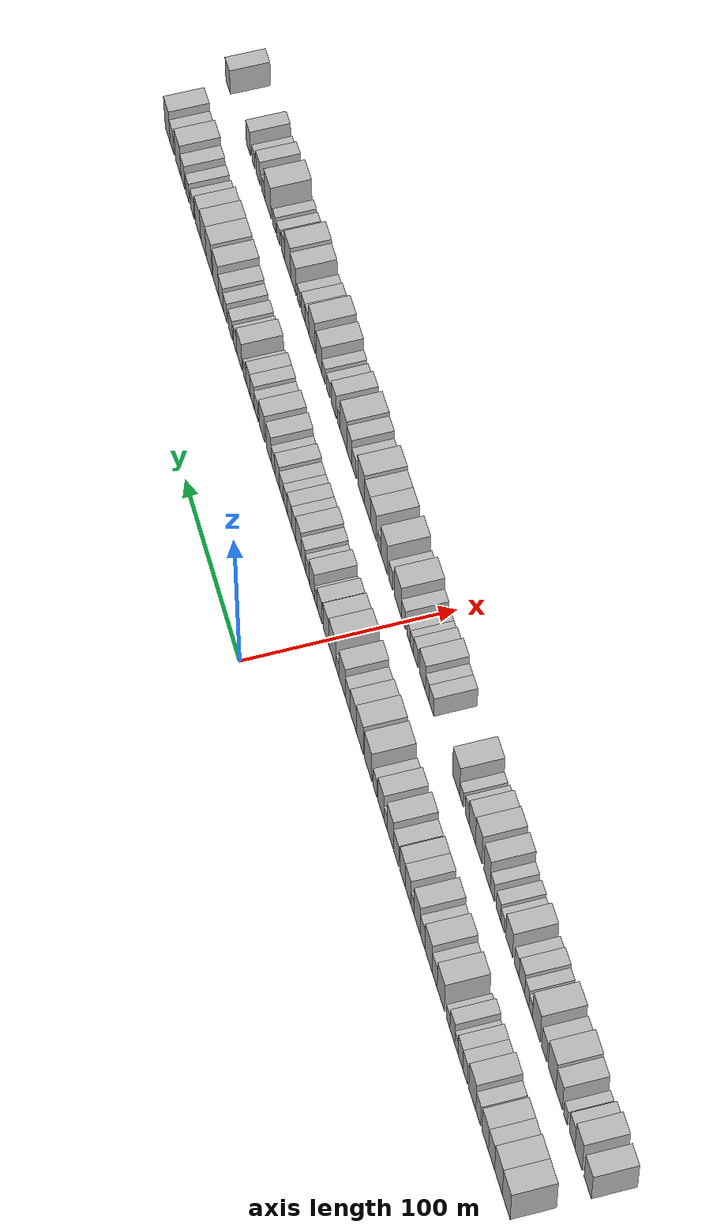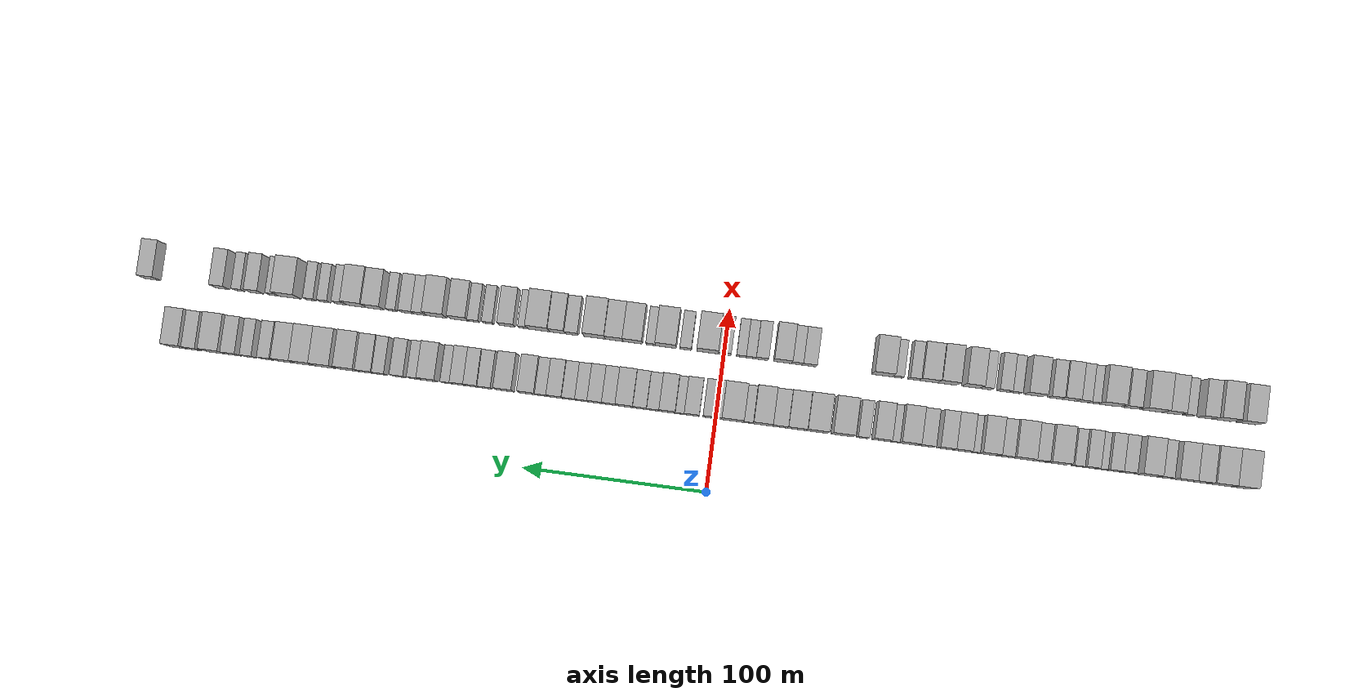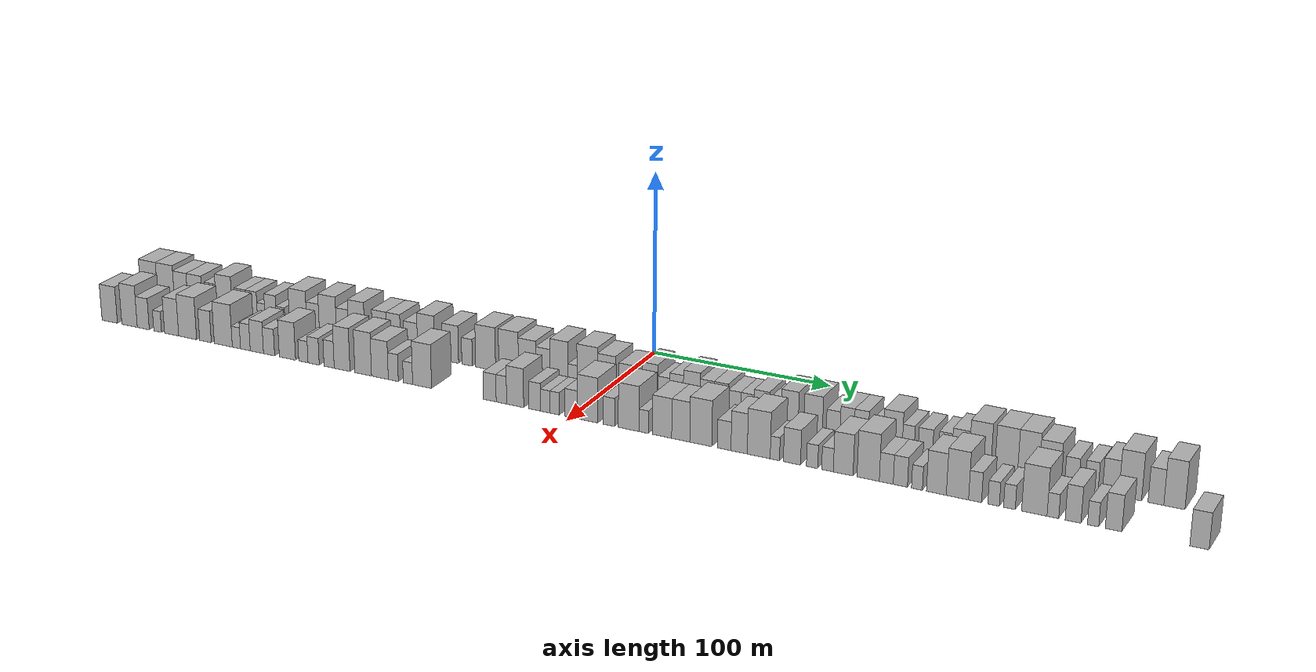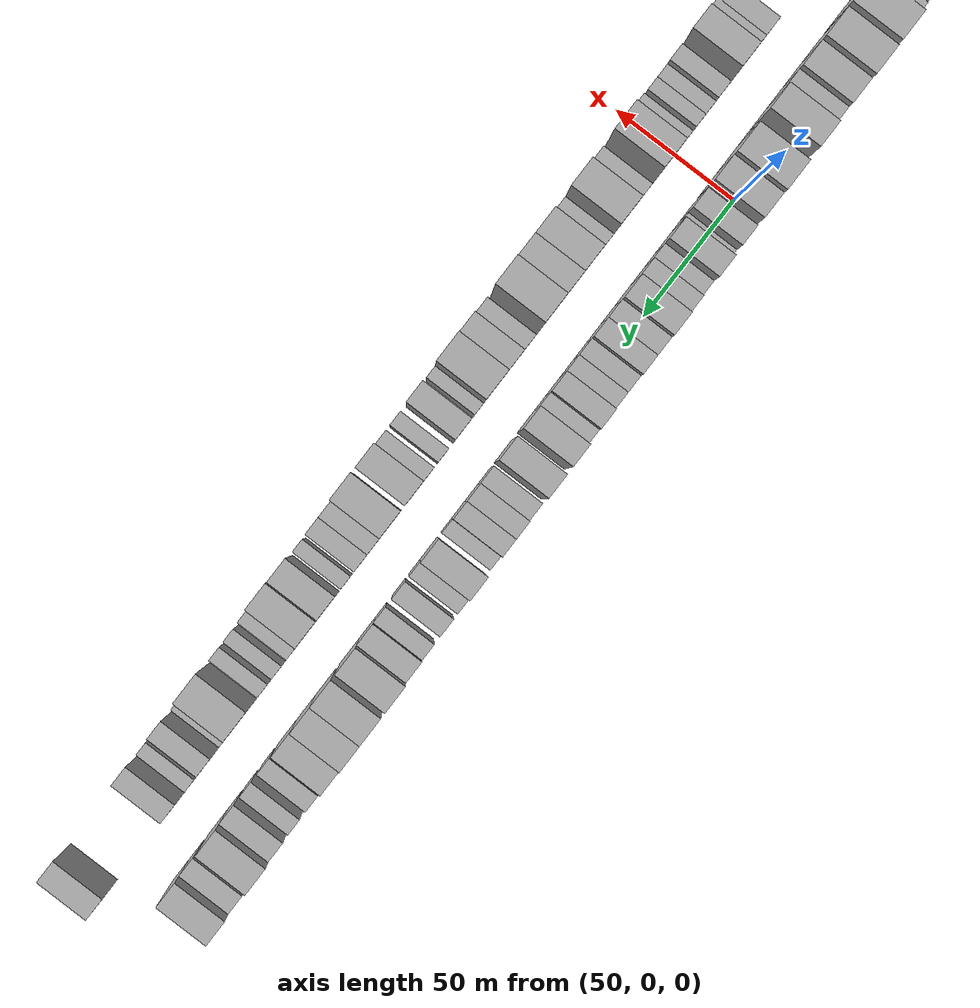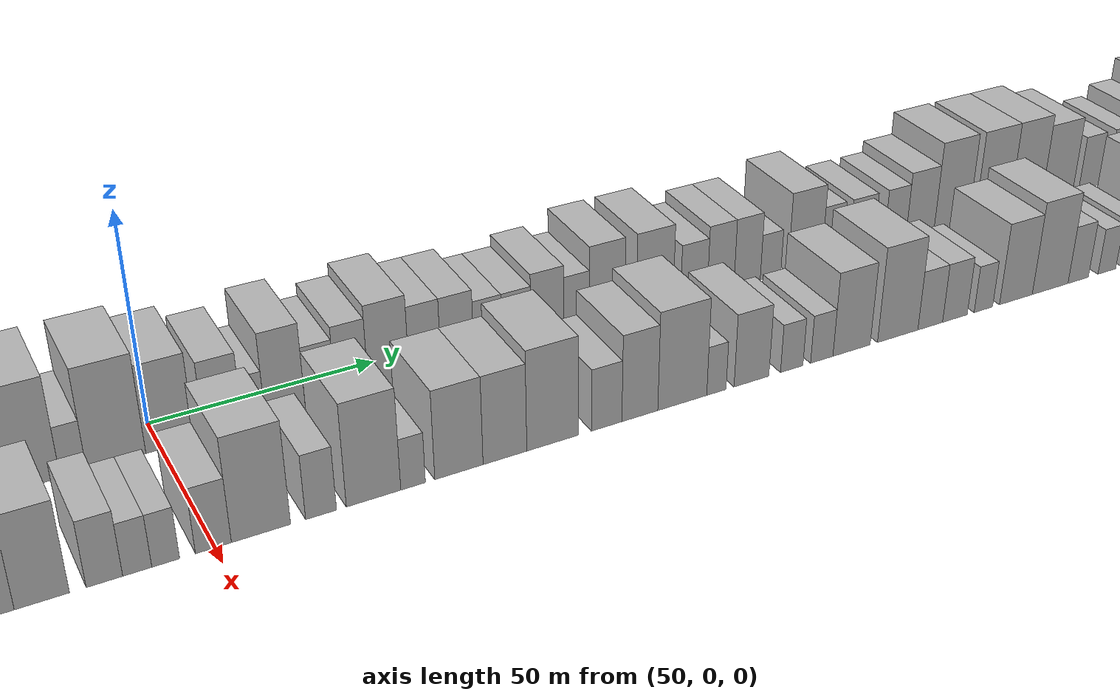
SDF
<sdf version="1.6">
 <world name="default">
  <scene>
   <sky><clouds><speed>12</speed></clouds></sky>
   <ambient>0.4 0.4 0.4 1</ambient>
   <background>0.7 0.7 0.7 1</background>
   <shadows>1</shadows>
  </scene>
  <gravity>0 0 -9.8066</gravity>
  <magnetic_field>6e-06 2.3e-05 -4.2e-05</magnetic_field>
  <physics default="0" name="default_physics" type="ode">
   <ode>
    <solver>
     <type>quick</type>
     <iters>10</iters>
     <sor>1.0</sor>
     <use_dynamic_moi_rescaling>0</use_dynamic_moi_rescaling>
    </solver>
    <constraints>
     <cfm>0</cfm>
     <erp>0.2</erp>
     <contact_max_correcting_vel>100</contact_max_correcting_vel>
     <contact_surface_layer>0.001</contact_surface_layer>
    </constraints>
   </ode>
   <max_step_size>0.004</max_step_size>
   <real_time_factor>1</real_time_factor>
   <real_time_update_rate>250</real_time_update_rate>
  </physics>
  <light name="sun" type="directional">
   <pose>0 0 10 0 0 0</pose>
   <diffuse>0.8 0.8 0.8 1</diffuse>
   <specular>0.2 0.2 0.2 1</specular>
   <attenuation>
    <range>1000</range>
    <constant>0.9</constant>
    <linear>0.01</linear>
    <quadratic>0.001</quadratic>
   </attenuation>
   <direction>-0.5 0.1 -0.9</direction>
  </light>
  <model name="building_1">
   <static>1</static>
   <pose>50.0000 -284.1968 0 0.000000 0.000000 0.000000</pose>
   <link name="link">
    <pose>0 0 12.00 0 0 0</pose>
    <collision name="collision"><geometry><box><size>20.0000 11.6064 24.0000</size></box></geometry></collision>
    <visual name="visual">
     <cast_shadows>0</cast_shadows>
     <geometry><box><size>20.0000 11.6064 24.0000</size></box></geometry>
     <material>
      <script>
       <uri>model://HANNAS_wall/materials/scripts</uri>
       <uri>model://HANNAS_wall/materials/textures</uri>
       <name>vrc/HANNAS_wall</name>
      </script>
     </material>
    </visual>
   </link>
  </model>
  <model name="building_2">
   <static>1</static>
   <pose>50.0000 -272.6836 0 0.000000 0.000000 0.000000</pose>
   <link name="link">
    <pose>0 0 12.00 0 0 0</pose>
    <collision name="collision"><geometry><box><size>20.0000 11.4199 24.0000</size></box></geometry></collision>
    <visual name="visual">
     <cast_shadows>0</cast_shadows>
     <geometry><box><size>20.0000 11.4199 24.0000</size></box></geometry>
     <material>
      <script>
       <uri>model://HANNAS_wall/materials/scripts</uri>
       <uri>model://HANNAS_wall/materials/textures</uri>
       <name>vrc/HANNAS_wall</name>
      </script>
     </material>
    </visual>
   </link>
  </model>
  <model name="building_3">
   <static>1</static>
   <pose>50.0000 -262.4343 0 0.000000 0.000000 0.000000</pose>
   <link name="link">
    <pose>0 0 10.50 0 0 0</pose>
    <collision name="collision"><geometry><box><size>20.0000 9.0788 21.0000</size></box></geometry></collision>
    <visual name="visual">
     <cast_shadows>0</cast_shadows>
     <geometry><box><size>20.0000 9.0788 21.0000</size></box></geometry>
     <material>
      <script>
       <uri>model://HANNAS_wall/materials/scripts</uri>
       <uri>model://HANNAS_wall/materials/textures</uri>
       <name>vrc/HANNAS_wall</name>
      </script>
     </material>
    </visual>
   </link>
  </model>
  <model name="building_4">
   <static>1</static>
   <pose>50.0000 -252.9656 0 0.000000 0.000000 0.000000</pose>
   <link name="link">
    <pose>0 0 10.50 0 0 0</pose>
    <collision name="collision"><geometry><box><size>20.0000 9.8587 21.0000</size></box></geometry></collision>
    <visual name="visual">
     <cast_shadows>0</cast_shadows>
     <geometry><box><size>20.0000 9.8587 21.0000</size></box></geometry>
     <material>
      <script>
       <uri>model://HANNAS_wall/materials/scripts</uri>
       <uri>model://HANNAS_wall/materials/textures</uri>
       <name>vrc/HANNAS_wall</name>
      </script>
     </material>
    </visual>
   </link>
  </model>
  <model name="building_5">
   <static>1</static>
   <pose>50.0000 -242.3682 0 0.000000 0.000000 0.000000</pose>
   <link name="link">
    <pose>0 0 9.00 0 0 0</pose>
    <collision name="collision"><geometry><box><size>20.0000 7.3362 18.0000</size></box></geometry></collision>
    <visual name="visual">
     <cast_shadows>0</cast_shadows>
     <geometry><box><size>20.0000 7.3362 18.0000</size></box></geometry>
     <material>
      <script>
       <uri>model://HANNAS_wall/materials/scripts</uri>
       <uri>model://HANNAS_wall/materials/textures</uri>
       <name>vrc/HANNAS_wall</name>
      </script>
     </material>
    </visual>
   </link>
  </model>
  <model name="building_6">
   <static>1</static>
   <pose>50.0000 -233.4100 0 0.000000 0.000000 0.000000</pose>
   <link name="link">
    <pose>0 0 12.00 0 0 0</pose>
    <collision name="collision"><geometry><box><size>20.0000 10.5801 24.0000</size></box></geometry></collision>
    <visual name="visual">
     <cast_shadows>0</cast_shadows>
     <geometry><box><size>20.0000 10.5801 24.0000</size></box></geometry>
     <material>
      <script>
       <uri>model://HANNAS_wall/materials/scripts</uri>
       <uri>model://HANNAS_wall/materials/textures</uri>
       <name>vrc/HANNAS_wall</name>
      </script>
     </material>
    </visual>
   </link>
  </model>
  <model name="building_7">
   <static>1</static>
   <pose>50.0000 -222.5193 0 0.000000 0.000000 0.000000</pose>
   <link name="link">
    <pose>0 0 9.00 0 0 0</pose>
    <collision name="collision"><geometry><box><size>20.0000 7.2013 18.0000</size></box></geometry></collision>
    <visual name="visual">
     <cast_shadows>0</cast_shadows>
     <geometry><box><size>20.0000 7.2013 18.0000</size></box></geometry>
     <material>
      <script>
       <uri>model://HANNAS_wall/materials/scripts</uri>
       <uri>model://HANNAS_wall/materials/textures</uri>
       <name>vrc/HANNAS_wall</name>
      </script>
     </material>
    </visual>
   </link>
  </model>
  <model name="building_8">
   <static>1</static>
   <pose>50.0000 -215.2438 0 0.000000 0.000000 0.000000</pose>
   <link name="link">
    <pose>0 0 9.00 0 0 0</pose>
    <collision name="collision"><geometry><box><size>20.0000 7.3496 18.0000</size></box></geometry></collision>
    <visual name="visual">
     <cast_shadows>0</cast_shadows>
     <geometry><box><size>20.0000 7.3496 18.0000</size></box></geometry>
     <material>
      <script>
       <uri>model://HANNAS_wall/materials/scripts</uri>
       <uri>model://HANNAS_wall/materials/textures</uri>
       <name>vrc/HANNAS_wall</name>
      </script>
     </material>
    </visual>
   </link>
  </model>
  <model name="building_9">
   <static>1</static>
   <pose>50.0000 -209.0613 0 0.000000 0.000000 0.000000</pose>
   <link name="link">
    <pose>0 0 6.00 0 0 0</pose>
    <collision name="collision"><geometry><box><size>20.0000 5.0154 12.0000</size></box></geometry></collision>
    <visual name="visual">
     <cast_shadows>0</cast_shadows>
     <geometry><box><size>20.0000 5.0154 12.0000</size></box></geometry>
     <material>
      <script>
       <uri>model://HANNAS_wall/materials/scripts</uri>
       <uri>model://HANNAS_wall/materials/textures</uri>
       <name>vrc/HANNAS_wall</name>
      </script>
     </material>
    </visual>
   </link>
  </model>
  <model name="building_10">
   <static>1</static>
   <pose>50.0000 -202.8698 0 0.000000 0.000000 0.000000</pose>
   <link name="link">
    <pose>0 0 9.00 0 0 0</pose>
    <collision name="collision"><geometry><box><size>20.0000 7.3677 18.0000</size></box></geometry></collision>
    <visual name="visual">
     <cast_shadows>0</cast_shadows>
     <geometry><box><size>20.0000 7.3677 18.0000</size></box></geometry>
     <material>
      <script>
       <uri>model://HANNAS_wall/materials/scripts</uri>
       <uri>model://HANNAS_wall/materials/textures</uri>
       <name>vrc/HANNAS_wall</name>
      </script>
     </material>
    </visual>
   </link>
  </model>
  <model name="building_11">
   <static>1</static>
   <pose>50.0000 -196.3837 0 0.000000 0.000000 0.000000</pose>
   <link name="link">
    <pose>0 0 6.00 0 0 0</pose>
    <collision name="collision"><geometry><box><size>20.0000 5.6044 12.0000</size></box></geometry></collision>
    <visual name="visual">
     <cast_shadows>0</cast_shadows>
     <geometry><box><size>20.0000 5.6044 12.0000</size></box></geometry>
     <material>
      <script>
       <uri>model://HANNAS_wall/materials/scripts</uri>
       <uri>model://HANNAS_wall/materials/textures</uri>
       <name>vrc/HANNAS_wall</name>
      </script>
     </material>
    </visual>
   </link>
  </model>
  <model name="building_12">
   <static>1</static>
   <pose>50.0000 -185.0307 0 0.000000 0.000000 0.000000</pose>
   <link name="link">
    <pose>0 0 12.00 0 0 0</pose>
    <collision name="collision"><geometry><box><size>20.0000 11.1017 24.0000</size></box></geometry></collision>
    <visual name="visual">
     <cast_shadows>0</cast_shadows>
     <geometry><box><size>20.0000 11.1017 24.0000</size></box></geometry>
     <material>
      <script>
       <uri>model://HANNAS_wall/materials/scripts</uri>
       <uri>model://HANNAS_wall/materials/textures</uri>
       <name>vrc/HANNAS_wall</name>
      </script>
     </material>
    </visual>
   </link>
  </model>
  <model name="building_13">
   <static>1</static>
   <pose>50.0000 -175.4873 0 0.000000 0.000000 0.000000</pose>
   <link name="link">
    <pose>0 0 9.00 0 0 0</pose>
    <collision name="collision"><geometry><box><size>20.0000 7.9851 18.0000</size></box></geometry></collision>
    <visual name="visual">
     <cast_shadows>0</cast_shadows>
     <geometry><box><size>20.0000 7.9851 18.0000</size></box></geometry>
     <material>
      <script>
       <uri>model://HANNAS_wall/materials/scripts</uri>
       <uri>model://HANNAS_wall/materials/textures</uri>
       <name>vrc/HANNAS_wall</name>
      </script>
     </material>
    </visual>
   </link>
  </model>
  <model name="building_14">
   <static>1</static>
   <pose>50.0000 -166.0058 0 0.000000 0.000000 0.000000</pose>
   <link name="link">
    <pose>0 0 12.00 0 0 0</pose>
    <collision name="collision"><geometry><box><size>20.0000 10.9779 24.0000</size></box></geometry></collision>
    <visual name="visual">
     <cast_shadows>0</cast_shadows>
     <geometry><box><size>20.0000 10.9779 24.0000</size></box></geometry>
     <material>
      <script>
       <uri>model://HANNAS_wall/materials/scripts</uri>
       <uri>model://HANNAS_wall/materials/textures</uri>
       <name>vrc/HANNAS_wall</name>
      </script>
     </material>
    </visual>
   </link>
  </model>
  <model name="building_15">
   <static>1</static>
   <pose>50.0000 -156.6610 0 0.000000 0.000000 0.000000</pose>
   <link name="link">
    <pose>0 0 9.00 0 0 0</pose>
    <collision name="collision"><geometry><box><size>20.0000 7.7117 18.0000</size></box></geometry></collision>
    <visual name="visual">
     <cast_shadows>0</cast_shadows>
     <geometry><box><size>20.0000 7.7117 18.0000</size></box></geometry>
     <material>
      <script>
       <uri>model://HANNAS_wall/materials/scripts</uri>
       <uri>model://HANNAS_wall/materials/textures</uri>
       <name>vrc/HANNAS_wall</name>
      </script>
     </material>
    </visual>
   </link>
  </model>
  <model name="building_16">
   <static>1</static>
   <pose>50.0000 -147.7419 0 0.000000 0.000000 0.000000</pose>
   <link name="link">
    <pose>0 0 12.00 0 0 0</pose>
    <collision name="collision"><geometry><box><size>20.0000 10.1264 24.0000</size></box></geometry></collision>
    <visual name="visual">
     <cast_shadows>0</cast_shadows>
     <geometry><box><size>20.0000 10.1264 24.0000</size></box></geometry>
     <material>
      <script>
       <uri>model://HANNAS_wall/materials/scripts</uri>
       <uri>model://HANNAS_wall/materials/textures</uri>
       <name>vrc/HANNAS_wall</name>
      </script>
     </material>
    </visual>
   </link>
  </model>
  <model name="building_17">
   <static>1</static>
   <pose>50.0000 -140.2602 0 0.000000 0.000000 0.000000</pose>
   <link name="link">
    <pose>0 0 6.00 0 0 0</pose>
    <collision name="collision"><geometry><box><size>20.0000 4.8370 12.0000</size></box></geometry></collision>
    <visual name="visual">
     <cast_shadows>0</cast_shadows>
     <geometry><box><size>20.0000 4.8370 12.0000</size></box></geometry>
     <material>
      <script>
       <uri>model://HANNAS_wall/materials/scripts</uri>
       <uri>model://HANNAS_wall/materials/textures</uri>
       <name>vrc/HANNAS_wall</name>
      </script>
     </material>
    </visual>
   </link>
  </model>
  <model name="building_18">
   <static>1</static>
   <pose>50.0000 -133.3484 0 0.000000 0.000000 0.000000</pose>
   <link name="link">
    <pose>0 0 10.50 0 0 0</pose>
    <collision name="collision"><geometry><box><size>20.0000 8.9866 21.0000</size></box></geometry></collision>
    <visual name="visual">
     <cast_shadows>0</cast_shadows>
     <geometry><box><size>20.0000 8.9866 21.0000</size></box></geometry>
     <material>
      <script>
       <uri>model://HANNAS_wall/materials/scripts</uri>
       <uri>model://HANNAS_wall/materials/textures</uri>
       <name>vrc/HANNAS_wall</name>
      </script>
     </material>
    </visual>
   </link>
  </model>
  <model name="building_19">
   <static>1</static>
   <pose>50.0000 -124.6117 0 0.000000 0.000000 0.000000</pose>
   <link name="link">
    <pose>0 0 10.50 0 0 0</pose>
    <collision name="collision"><geometry><box><size>20.0000 8.4868 21.0000</size></box></geometry></collision>
    <visual name="visual">
     <cast_shadows>0</cast_shadows>
     <geometry><box><size>20.0000 8.4868 21.0000</size></box></geometry>
     <material>
      <script>
       <uri>model://HANNAS_wall/materials/scripts</uri>
       <uri>model://HANNAS_wall/materials/textures</uri>
       <name>vrc/HANNAS_wall</name>
      </script>
     </material>
    </visual>
   </link>
  </model>
  <model name="building_20">
   <static>1</static>
   <pose>50.0000 -114.1326 0 0.000000 0.000000 0.000000</pose>
   <link name="link">
    <pose>0 0 9.00 0 0 0</pose>
    <collision name="collision"><geometry><box><size>20.0000 8.4714 18.0000</size></box></geometry></collision>
    <visual name="visual">
     <cast_shadows>0</cast_shadows>
     <geometry><box><size>20.0000 8.4714 18.0000</size></box></geometry>
     <material>
      <script>
       <uri>model://HANNAS_wall/materials/scripts</uri>
       <uri>model://HANNAS_wall/materials/textures</uri>
       <name>vrc/HANNAS_wall</name>
      </script>
     </material>
    </visual>
   </link>
  </model>
  <model name="building_21">
   <static>1</static>
   <pose>50.0000 -104.7004 0 0.000000 0.000000 0.000000</pose>
   <link name="link">
    <pose>0 0 12.00 0 0 0</pose>
    <collision name="collision"><geometry><box><size>20.0000 10.3930 24.0000</size></box></geometry></collision>
    <visual name="visual">
     <cast_shadows>0</cast_shadows>
     <geometry><box><size>20.0000 10.3930 24.0000</size></box></geometry>
     <material>
      <script>
       <uri>model://HANNAS_wall/materials/scripts</uri>
       <uri>model://HANNAS_wall/materials/textures</uri>
       <name>vrc/HANNAS_wall</name>
      </script>
     </material>
    </visual>
   </link>
  </model>
  <model name="building_22">
   <static>1</static>
   <pose>50.0000 -97.0555 0 0.000000 0.000000 0.000000</pose>
   <link name="link">
    <pose>0 0 6.00 0 0 0</pose>
    <collision name="collision"><geometry><box><size>20.0000 4.8968 12.0000</size></box></geometry></collision>
    <visual name="visual">
     <cast_shadows>0</cast_shadows>
     <geometry><box><size>20.0000 4.8968 12.0000</size></box></geometry>
     <material>
      <script>
       <uri>model://HANNAS_wall/materials/scripts</uri>
       <uri>model://HANNAS_wall/materials/textures</uri>
       <name>vrc/HANNAS_wall</name>
      </script>
     </material>
    </visual>
   </link>
  </model>
  <model name="building_23">
   <static>1</static>
   <pose>50.0000 -89.8188 0 0.000000 0.000000 0.000000</pose>
   <link name="link">
    <pose>0 0 10.50 0 0 0</pose>
    <collision name="collision"><geometry><box><size>20.0000 9.5765 21.0000</size></box></geometry></collision>
    <visual name="visual">
     <cast_shadows>0</cast_shadows>
     <geometry><box><size>20.0000 9.5765 21.0000</size></box></geometry>
     <material>
      <script>
       <uri>model://HANNAS_wall/materials/scripts</uri>
       <uri>model://HANNAS_wall/materials/textures</uri>
       <name>vrc/HANNAS_wall</name>
      </script>
     </material>
    </visual>
   </link>
  </model>
  <model name="building_24">
   <static>1</static>
   <pose>50.0000 -79.8754 0 0.000000 0.000000 0.000000</pose>
   <link name="link">
    <pose>0 0 7.50 0 0 0</pose>
    <collision name="collision"><geometry><box><size>20.0000 6.3102 15.0000</size></box></geometry></collision>
    <visual name="visual">
     <cast_shadows>0</cast_shadows>
     <geometry><box><size>20.0000 6.3102 15.0000</size></box></geometry>
     <material>
      <script>
       <uri>model://HANNAS_wall/materials/scripts</uri>
       <uri>model://HANNAS_wall/materials/textures</uri>
       <name>vrc/HANNAS_wall</name>
      </script>
     </material>
    </visual>
   </link>
  </model>
  <model name="building_25">
   <static>1</static>
   <pose>50.0000 -68.7800 0 0.000000 0.000000 0.000000</pose>
   <link name="link">
    <pose>0 0 12.00 0 0 0</pose>
    <collision name="collision"><geometry><box><size>20.0000 11.8807 24.0000</size></box></geometry></collision>
    <visual name="visual">
     <cast_shadows>0</cast_shadows>
     <geometry><box><size>20.0000 11.8807 24.0000</size></box></geometry>
     <material>
      <script>
       <uri>model://HANNAS_wall/materials/scripts</uri>
       <uri>model://HANNAS_wall/materials/textures</uri>
       <name>vrc/HANNAS_wall</name>
      </script>
     </material>
    </visual>
   </link>
  </model>
  <model name="building_26">
   <static>1</static>
   <pose>50.0000 -55.0351 0 0.000000 0.000000 0.000000</pose>
   <link name="link">
    <pose>0 0 12.00 0 0 0</pose>
    <collision name="collision"><geometry><box><size>20.0000 11.6092 24.0000</size></box></geometry></collision>
    <visual name="visual">
     <cast_shadows>0</cast_shadows>
     <geometry><box><size>20.0000 11.6092 24.0000</size></box></geometry>
     <material>
      <script>
       <uri>model://HANNAS_wall/materials/scripts</uri>
       <uri>model://HANNAS_wall/materials/textures</uri>
       <name>vrc/HANNAS_wall</name>
      </script>
     </material>
    </visual>
   </link>
  </model>
  <model name="building_27">
   <static>1</static>
   <pose>50.0000 -44.1194 0 0.000000 0.000000 0.000000</pose>
   <link name="link">
    <pose>0 0 10.50 0 0 0</pose>
    <collision name="collision"><geometry><box><size>20.0000 10.2222 21.0000</size></box></geometry></collision>
    <visual name="visual">
     <cast_shadows>0</cast_shadows>
     <geometry><box><size>20.0000 10.2222 21.0000</size></box></geometry>
     <material>
      <script>
       <uri>model://HANNAS_wall/materials/scripts</uri>
       <uri>model://HANNAS_wall/materials/textures</uri>
       <name>vrc/HANNAS_wall</name>
      </script>
     </material>
    </visual>
   </link>
  </model>
  <model name="building_28">
   <static>1</static>
   <pose>50.0000 -34.8238 0 0.000000 0.000000 0.000000</pose>
   <link name="link">
    <pose>0 0 9.00 0 0 0</pose>
    <collision name="collision"><geometry><box><size>20.0000 8.3691 18.0000</size></box></geometry></collision>
    <visual name="visual">
     <cast_shadows>0</cast_shadows>
     <geometry><box><size>20.0000 8.3691 18.0000</size></box></geometry>
     <material>
      <script>
       <uri>model://HANNAS_wall/materials/scripts</uri>
       <uri>model://HANNAS_wall/materials/textures</uri>
       <name>vrc/HANNAS_wall</name>
      </script>
     </material>
    </visual>
   </link>
  </model>
  <model name="building_29">
   <static>1</static>
   <pose>50.0000 -25.4632 0 0.000000 0.000000 0.000000</pose>
   <link name="link">
    <pose>0 0 12.00 0 0 0</pose>
    <collision name="collision"><geometry><box><size>20.0000 10.3520 24.0000</size></box></geometry></collision>
    <visual name="visual">
     <cast_shadows>0</cast_shadows>
     <geometry><box><size>20.0000 10.3520 24.0000</size></box></geometry>
     <material>
      <script>
       <uri>model://HANNAS_wall/materials/scripts</uri>
       <uri>model://HANNAS_wall/materials/textures</uri>
       <name>vrc/HANNAS_wall</name>
      </script>
     </material>
    </visual>
   </link>
  </model>
  <model name="building_30">
   <static>1</static>
   <pose>50.0000 -17.6929 0 0.000000 0.000000 0.000000</pose>
   <link name="link">
    <pose>0 0 6.00 0 0 0</pose>
    <collision name="collision"><geometry><box><size>20.0000 5.1887 12.0000</size></box></geometry></collision>
    <visual name="visual">
     <cast_shadows>0</cast_shadows>
     <geometry><box><size>20.0000 5.1887 12.0000</size></box></geometry>
     <material>
      <script>
       <uri>model://HANNAS_wall/materials/scripts</uri>
       <uri>model://HANNAS_wall/materials/textures</uri>
       <name>vrc/HANNAS_wall</name>
      </script>
     </material>
    </visual>
   </link>
  </model>
  <model name="building_31">
   <static>1</static>
   <pose>50.0000 -9.1304 0 0.000000 0.000000 0.000000</pose>
   <link name="link">
    <pose>0 0 12.00 0 0 0</pose>
    <collision name="collision"><geometry><box><size>20.0000 11.9362 24.0000</size></box></geometry></collision>
    <visual name="visual">
     <cast_shadows>0</cast_shadows>
     <geometry><box><size>20.0000 11.9362 24.0000</size></box></geometry>
     <material>
      <script>
       <uri>model://HANNAS_wall/materials/scripts</uri>
       <uri>model://HANNAS_wall/materials/textures</uri>
       <name>vrc/HANNAS_wall</name>
      </script>
     </material>
    </visual>
   </link>
  </model>
  <model name="building_32">
   <static>1</static>
   <pose>50.0000 1.9001 0 0.000000 0.000000 0.000000</pose>
   <link name="link">
    <pose>0 0 10.50 0 0 0</pose>
    <collision name="collision"><geometry><box><size>20.0000 10.1247 21.0000</size></box></geometry></collision>
    <visual name="visual">
     <cast_shadows>0</cast_shadows>
     <geometry><box><size>20.0000 10.1247 21.0000</size></box></geometry>
     <material>
      <script>
       <uri>model://HANNAS_wall/materials/scripts</uri>
       <uri>model://HANNAS_wall/materials/textures</uri>
       <name>vrc/HANNAS_wall</name>
      </script>
     </material>
    </visual>
   </link>
  </model>
  <model name="building_33">
   <static>1</static>
   <pose>50.0000 13.0266 0 0.000000 0.000000 0.000000</pose>
   <link name="link">
    <pose>0 0 9.00 0 0 0</pose>
    <collision name="collision"><geometry><box><size>20.0000 8.1283 18.0000</size></box></geometry></collision>
    <visual name="visual">
     <cast_shadows>0</cast_shadows>
     <geometry><box><size>20.0000 8.1283 18.0000</size></box></geometry>
     <material>
      <script>
       <uri>model://HANNAS_wall/materials/scripts</uri>
       <uri>model://HANNAS_wall/materials/textures</uri>
       <name>vrc/HANNAS_wall</name>
      </script>
     </material>
    </visual>
   </link>
  </model>
  <model name="building_34">
   <static>1</static>
   <pose>50.0000 19.5175 0 0.000000 0.000000 0.000000</pose>
   <link name="link">
    <pose>0 0 6.00 0 0 0</pose>
    <collision name="collision"><geometry><box><size>20.0000 4.8535 12.0000</size></box></geometry></collision>
    <visual name="visual">
     <cast_shadows>0</cast_shadows>
     <geometry><box><size>20.0000 4.8535 12.0000</size></box></geometry>
     <material>
      <script>
       <uri>model://HANNAS_wall/materials/scripts</uri>
       <uri>model://HANNAS_wall/materials/textures</uri>
       <name>vrc/HANNAS_wall</name>
      </script>
     </material>
    </visual>
   </link>
  </model>
  <model name="building_35">
   <static>1</static>
   <pose>50.0000 26.3056 0 0.000000 0.000000 0.000000</pose>
   <link name="link">
    <pose>0 0 10.50 0 0 0</pose>
    <collision name="collision"><geometry><box><size>20.0000 8.7228 21.0000</size></box></geometry></collision>
    <visual name="visual">
     <cast_shadows>0</cast_shadows>
     <geometry><box><size>20.0000 8.7228 21.0000</size></box></geometry>
     <material>
      <script>
       <uri>model://HANNAS_wall/materials/scripts</uri>
       <uri>model://HANNAS_wall/materials/textures</uri>
       <name>vrc/HANNAS_wall</name>
      </script>
     </material>
    </visual>
   </link>
  </model>
  <model name="building_36">
   <static>1</static>
   <pose>50.0000 34.0300 0 0.000000 0.000000 0.000000</pose>
   <link name="link">
    <pose>0 0 7.50 0 0 0</pose>
    <collision name="collision"><geometry><box><size>20.0000 6.7259 15.0000</size></box></geometry></collision>
    <visual name="visual">
     <cast_shadows>0</cast_shadows>
     <geometry><box><size>20.0000 6.7259 15.0000</size></box></geometry>
     <material>
      <script>
       <uri>model://HANNAS_wall/materials/scripts</uri>
       <uri>model://HANNAS_wall/materials/textures</uri>
       <name>vrc/HANNAS_wall</name>
      </script>
     </material>
    </visual>
   </link>
  </model>
  <model name="building_37">
   <static>1</static>
   <pose>50.0000 41.0976 0 0.000000 0.000000 0.000000</pose>
   <link name="link">
    <pose>0 0 9.00 0 0 0</pose>
    <collision name="collision"><geometry><box><size>20.0000 7.4093 18.0000</size></box></geometry></collision>
    <visual name="visual">
     <cast_shadows>0</cast_shadows>
     <geometry><box><size>20.0000 7.4093 18.0000</size></box></geometry>
     <material>
      <script>
       <uri>model://HANNAS_wall/materials/scripts</uri>
       <uri>model://HANNAS_wall/materials/textures</uri>
       <name>vrc/HANNAS_wall</name>
      </script>
     </material>
    </visual>
   </link>
  </model>
  <model name="building_38">
   <static>1</static>
   <pose>50.0000 49.4963 0 0.000000 0.000000 0.000000</pose>
   <link name="link">
    <pose>0 0 10.50 0 0 0</pose>
    <collision name="collision"><geometry><box><size>20.0000 9.3881 21.0000</size></box></geometry></collision>
    <visual name="visual">
     <cast_shadows>0</cast_shadows>
     <geometry><box><size>20.0000 9.3881 21.0000</size></box></geometry>
     <material>
      <script>
       <uri>model://HANNAS_wall/materials/scripts</uri>
       <uri>model://HANNAS_wall/materials/textures</uri>
       <name>vrc/HANNAS_wall</name>
      </script>
     </material>
    </visual>
   </link>
  </model>
  <model name="building_39">
   <static>1</static>
   <pose>50.0000 57.9015 0 0.000000 0.000000 0.000000</pose>
   <link name="link">
    <pose>0 0 9.00 0 0 0</pose>
    <collision name="collision"><geometry><box><size>20.0000 7.4222 18.0000</size></box></geometry></collision>
    <visual name="visual">
     <cast_shadows>0</cast_shadows>
     <geometry><box><size>20.0000 7.4222 18.0000</size></box></geometry>
     <material>
      <script>
       <uri>model://HANNAS_wall/materials/scripts</uri>
       <uri>model://HANNAS_wall/materials/textures</uri>
       <name>vrc/HANNAS_wall</name>
      </script>
     </material>
    </visual>
   </link>
  </model>
  <model name="building_40">
   <static>1</static>
   <pose>50.0000 65.5200 0 0.000000 0.000000 0.000000</pose>
   <link name="link">
    <pose>0 0 9.00 0 0 0</pose>
    <collision name="collision"><geometry><box><size>20.0000 7.8149 18.0000</size></box></geometry></collision>
    <visual name="visual">
     <cast_shadows>0</cast_shadows>
     <geometry><box><size>20.0000 7.8149 18.0000</size></box></geometry>
     <material>
      <script>
       <uri>model://HANNAS_wall/materials/scripts</uri>
       <uri>model://HANNAS_wall/materials/textures</uri>
       <name>vrc/HANNAS_wall</name>
      </script>
     </material>
    </visual>
   </link>
  </model>
  <model name="building_41">
   <static>1</static>
   <pose>50.0000 72.8399 0 0.000000 0.000000 0.000000</pose>
   <link name="link">
    <pose>0 0 7.50 0 0 0</pose>
    <collision name="collision"><geometry><box><size>20.0000 6.8249 15.0000</size></box></geometry></collision>
    <visual name="visual">
     <cast_shadows>0</cast_shadows>
     <geometry><box><size>20.0000 6.8249 15.0000</size></box></geometry>
     <material>
      <script>
       <uri>model://HANNAS_wall/materials/scripts</uri>
       <uri>model://HANNAS_wall/materials/textures</uri>
       <name>vrc/HANNAS_wall</name>
      </script>
     </material>
    </visual>
   </link>
  </model>
  <model name="building_42">
   <static>1</static>
   <pose>50.0000 79.7931 0 0.000000 0.000000 0.000000</pose>
   <link name="link">
    <pose>0 0 7.50 0 0 0</pose>
    <collision name="collision"><geometry><box><size>20.0000 7.0817 15.0000</size></box></geometry></collision>
    <visual name="visual">
     <cast_shadows>0</cast_shadows>
     <geometry><box><size>20.0000 7.0817 15.0000</size></box></geometry>
     <material>
      <script>
       <uri>model://HANNAS_wall/materials/scripts</uri>
       <uri>model://HANNAS_wall/materials/textures</uri>
       <name>vrc/HANNAS_wall</name>
      </script>
     </material>
    </visual>
   </link>
  </model>
  <model name="building_43">
   <static>1</static>
   <pose>50.0000 87.4263 0 0.000000 0.000000 0.000000</pose>
   <link name="link">
    <pose>0 0 9.00 0 0 0</pose>
    <collision name="collision"><geometry><box><size>20.0000 8.1846 18.0000</size></box></geometry></collision>
    <visual name="visual">
     <cast_shadows>0</cast_shadows>
     <geometry><box><size>20.0000 8.1846 18.0000</size></box></geometry>
     <material>
      <script>
       <uri>model://HANNAS_wall/materials/scripts</uri>
       <uri>model://HANNAS_wall/materials/textures</uri>
       <name>vrc/HANNAS_wall</name>
      </script>
     </material>
    </visual>
   </link>
  </model>
  <model name="building_44">
   <static>1</static>
   <pose>50.0000 94.6946 0 0.000000 0.000000 0.000000</pose>
   <link name="link">
    <pose>0 0 7.50 0 0 0</pose>
    <collision name="collision"><geometry><box><size>20.0000 6.3521 15.0000</size></box></geometry></collision>
    <visual name="visual">
     <cast_shadows>0</cast_shadows>
     <geometry><box><size>20.0000 6.3521 15.0000</size></box></geometry>
     <material>
      <script>
       <uri>model://HANNAS_wall/materials/scripts</uri>
       <uri>model://HANNAS_wall/materials/textures</uri>
       <name>vrc/HANNAS_wall</name>
      </script>
     </material>
    </visual>
   </link>
  </model>
  <model name="building_45">
   <static>1</static>
   <pose>50.0000 102.4295 0 0.000000 0.000000 0.000000</pose>
   <link name="link">
    <pose>0 0 10.50 0 0 0</pose>
    <collision name="collision"><geometry><box><size>20.0000 9.1175 21.0000</size></box></geometry></collision>
    <visual name="visual">
     <cast_shadows>0</cast_shadows>
     <geometry><box><size>20.0000 9.1175 21.0000</size></box></geometry>
     <material>
      <script>
       <uri>model://HANNAS_wall/materials/scripts</uri>
       <uri>model://HANNAS_wall/materials/textures</uri>
       <name>vrc/HANNAS_wall</name>
      </script>
     </material>
    </visual>
   </link>
  </model>
  <model name="building_46">
   <static>1</static>
   <pose>50.0000 114.8611 0 0.000000 0.000000 0.000000</pose>
   <link name="link">
    <pose>0 0 10.50 0 0 0</pose>
    <collision name="collision"><geometry><box><size>20.0000 9.7458 21.0000</size></box></geometry></collision>
    <visual name="visual">
     <cast_shadows>0</cast_shadows>
     <geometry><box><size>20.0000 9.7458 21.0000</size></box></geometry>
     <material>
      <script>
       <uri>model://HANNAS_wall/materials/scripts</uri>
       <uri>model://HANNAS_wall/materials/textures</uri>
       <name>vrc/HANNAS_wall</name>
      </script>
     </material>
    </visual>
   </link>
  </model>
  <model name="building_47">
   <static>1</static>
   <pose>50.0000 125.3384 0 0.000000 0.000000 0.000000</pose>
   <link name="link">
    <pose>0 0 7.50 0 0 0</pose>
    <collision name="collision"><geometry><box><size>20.0000 7.2088 15.0000</size></box></geometry></collision>
    <visual name="visual">
     <cast_shadows>0</cast_shadows>
     <geometry><box><size>20.0000 7.2088 15.0000</size></box></geometry>
     <material>
      <script>
       <uri>model://HANNAS_wall/materials/scripts</uri>
       <uri>model://HANNAS_wall/materials/textures</uri>
       <name>vrc/HANNAS_wall</name>
      </script>
     </material>
    </visual>
   </link>
  </model>
  <model name="building_48">
   <static>1</static>
   <pose>50.0000 132.5810 0 0.000000 0.000000 0.000000</pose>
   <link name="link">
    <pose>0 0 9.00 0 0 0</pose>
    <collision name="collision"><geometry><box><size>20.0000 7.2764 18.0000</size></box></geometry></collision>
    <visual name="visual">
     <cast_shadows>0</cast_shadows>
     <geometry><box><size>20.0000 7.2764 18.0000</size></box></geometry>
     <material>
      <script>
       <uri>model://HANNAS_wall/materials/scripts</uri>
       <uri>model://HANNAS_wall/materials/textures</uri>
       <name>vrc/HANNAS_wall</name>
      </script>
     </material>
    </visual>
   </link>
  </model>
  <model name="building_49">
   <static>1</static>
   <pose>50.0000 139.8819 0 0.000000 0.000000 0.000000</pose>
   <link name="link">
    <pose>0 0 9.00 0 0 0</pose>
    <collision name="collision"><geometry><box><size>20.0000 7.3253 18.0000</size></box></geometry></collision>
    <visual name="visual">
     <cast_shadows>0</cast_shadows>
     <geometry><box><size>20.0000 7.3253 18.0000</size></box></geometry>
     <material>
      <script>
       <uri>model://HANNAS_wall/materials/scripts</uri>
       <uri>model://HANNAS_wall/materials/textures</uri>
       <name>vrc/HANNAS_wall</name>
      </script>
     </material>
    </visual>
   </link>
  </model>
  <model name="building_50">
   <static>1</static>
   <pose>50.0000 146.4218 0 0.000000 0.000000 0.000000</pose>
   <link name="link">
    <pose>0 0 6.00 0 0 0</pose>
    <collision name="collision"><geometry><box><size>20.0000 5.7545 12.0000</size></box></geometry></collision>
    <visual name="visual">
     <cast_shadows>0</cast_shadows>
     <geometry><box><size>20.0000 5.7545 12.0000</size></box></geometry>
     <material>
      <script>
       <uri>model://HANNAS_wall/materials/scripts</uri>
       <uri>model://HANNAS_wall/materials/textures</uri>
       <name>vrc/HANNAS_wall</name>
      </script>
     </material>
    </visual>
   </link>
  </model>
  <model name="building_51">
   <static>1</static>
   <pose>50.0000 156.1290 0 0.000000 0.000000 0.000000</pose>
   <link name="link">
    <pose>0 0 10.50 0 0 0</pose>
    <collision name="collision"><geometry><box><size>20.0000 9.6599 21.0000</size></box></geometry></collision>
    <visual name="visual">
     <cast_shadows>0</cast_shadows>
     <geometry><box><size>20.0000 9.6599 21.0000</size></box></geometry>
     <material>
      <script>
       <uri>model://HANNAS_wall/materials/scripts</uri>
       <uri>model://HANNAS_wall/materials/textures</uri>
       <name>vrc/HANNAS_wall</name>
      </script>
     </material>
    </visual>
   </link>
  </model>
  <model name="building_52">
   <static>1</static>
   <pose>50.0000 163.9792 0 0.000000 0.000000 0.000000</pose>
   <link name="link">
    <pose>0 0 7.50 0 0 0</pose>
    <collision name="collision"><geometry><box><size>20.0000 6.0406 15.0000</size></box></geometry></collision>
    <visual name="visual">
     <cast_shadows>0</cast_shadows>
     <geometry><box><size>20.0000 6.0406 15.0000</size></box></geometry>
     <material>
      <script>
       <uri>model://HANNAS_wall/materials/scripts</uri>
       <uri>model://HANNAS_wall/materials/textures</uri>
       <name>vrc/HANNAS_wall</name>
      </script>
     </material>
    </visual>
   </link>
  </model>
  <model name="building_53">
   <static>1</static>
   <pose>50.0000 172.6620 0 0.000000 0.000000 0.000000</pose>
   <link name="link">
    <pose>0 0 7.50 0 0 0</pose>
    <collision name="collision"><geometry><box><size>20.0000 7.3249 15.0000</size></box></geometry></collision>
    <visual name="visual">
     <cast_shadows>0</cast_shadows>
     <geometry><box><size>20.0000 7.3249 15.0000</size></box></geometry>
     <material>
      <script>
       <uri>model://HANNAS_wall/materials/scripts</uri>
       <uri>model://HANNAS_wall/materials/textures</uri>
       <name>vrc/HANNAS_wall</name>
      </script>
     </material>
    </visual>
   </link>
  </model>
  <model name="building_54">
   <static>1</static>
   <pose>50.0000 182.6225 0 0.000000 0.000000 0.000000</pose>
   <link name="link">
    <pose>0 0 7.50 0 0 0</pose>
    <collision name="collision"><geometry><box><size>20.0000 6.5962 15.0000</size></box></geometry></collision>
    <visual name="visual">
     <cast_shadows>0</cast_shadows>
     <geometry><box><size>20.0000 6.5962 15.0000</size></box></geometry>
     <material>
      <script>
       <uri>model://HANNAS_wall/materials/scripts</uri>
       <uri>model://HANNAS_wall/materials/textures</uri>
       <name>vrc/HANNAS_wall</name>
      </script>
     </material>
    </visual>
   </link>
  </model>
  <model name="building_55">
   <static>1</static>
   <pose>50.0000 190.2507 0 0.000000 0.000000 0.000000</pose>
   <link name="link">
    <pose>0 0 9.00 0 0 0</pose>
    <collision name="collision"><geometry><box><size>20.0000 8.6602 18.0000</size></box></geometry></collision>
    <visual name="visual">
     <cast_shadows>0</cast_shadows>
     <geometry><box><size>20.0000 8.6602 18.0000</size></box></geometry>
     <material>
      <script>
       <uri>model://HANNAS_wall/materials/scripts</uri>
       <uri>model://HANNAS_wall/materials/textures</uri>
       <name>vrc/HANNAS_wall</name>
      </script>
     </material>
    </visual>
   </link>
  </model>
  <model name="building_56">
   <static>1</static>
   <pose>50.0000 199.9856 0 0.000000 0.000000 0.000000</pose>
   <link name="link">
    <pose>0 0 12.00 0 0 0</pose>
    <collision name="collision"><geometry><box><size>20.0000 10.8095 24.0000</size></box></geometry></collision>
    <visual name="visual">
     <cast_shadows>0</cast_shadows>
     <geometry><box><size>20.0000 10.8095 24.0000</size></box></geometry>
     <material>
      <script>
       <uri>model://HANNAS_wall/materials/scripts</uri>
       <uri>model://HANNAS_wall/materials/textures</uri>
       <name>vrc/HANNAS_wall</name>
      </script>
     </material>
    </visual>
   </link>
  </model>
  <model name="building_57">
   <static>1</static>
   <pose>50.0000 212.9404 0 0.000000 0.000000 0.000000</pose>
   <link name="link">
    <pose>0 0 12.00 0 0 0</pose>
    <collision name="collision"><geometry><box><size>20.0000 11.1001 24.0000</size></box></geometry></collision>
    <visual name="visual">
     <cast_shadows>0</cast_shadows>
     <geometry><box><size>20.0000 11.1001 24.0000</size></box></geometry>
     <material>
      <script>
       <uri>model://HANNAS_wall/materials/scripts</uri>
       <uri>model://HANNAS_wall/materials/textures</uri>
       <name>vrc/HANNAS_wall</name>
      </script>
     </material>
    </visual>
   </link>
  </model>
  <model name="building_58">
   <static>1</static>
   <pose>50.0000 223.7016 0 0.000000 0.000000 0.000000</pose>
   <link name="link">
    <pose>0 0 12.00 0 0 0</pose>
    <collision name="collision"><geometry><box><size>20.0000 10.4222 24.0000</size></box></geometry></collision>
    <visual name="visual">
     <cast_shadows>0</cast_shadows>
     <geometry><box><size>20.0000 10.4222 24.0000</size></box></geometry>
     <material>
      <script>
       <uri>model://HANNAS_wall/materials/scripts</uri>
       <uri>model://HANNAS_wall/materials/textures</uri>
       <name>vrc/HANNAS_wall</name>
      </script>
     </material>
    </visual>
   </link>
  </model>
  <model name="building_59">
   <static>1</static>
   <pose>50.0000 234.0878 0 0.000000 0.000000 0.000000</pose>
   <link name="link">
    <pose>0 0 10.50 0 0 0</pose>
    <collision name="collision"><geometry><box><size>20.0000 10.3503 21.0000</size></box></geometry></collision>
    <visual name="visual">
     <cast_shadows>0</cast_shadows>
     <geometry><box><size>20.0000 10.3503 21.0000</size></box></geometry>
     <material>
      <script>
       <uri>model://HANNAS_wall/materials/scripts</uri>
       <uri>model://HANNAS_wall/materials/textures</uri>
       <name>vrc/HANNAS_wall</name>
      </script>
     </material>
    </visual>
   </link>
  </model>
  <model name="building_60">
   <static>1</static>
   <pose>50.0000 244.6295 0 0.000000 0.000000 0.000000</pose>
   <link name="link">
    <pose>0 0 7.50 0 0 0</pose>
    <collision name="collision"><geometry><box><size>20.0000 6.7331 15.0000</size></box></geometry></collision>
    <visual name="visual">
     <cast_shadows>0</cast_shadows>
     <geometry><box><size>20.0000 6.7331 15.0000</size></box></geometry>
     <material>
      <script>
       <uri>model://HANNAS_wall/materials/scripts</uri>
       <uri>model://HANNAS_wall/materials/textures</uri>
       <name>vrc/HANNAS_wall</name>
      </script>
     </material>
    </visual>
   </link>
  </model>
  <model name="building_61">
   <static>1</static>
   <pose>50.0000 254.1523 0 0.000000 0.000000 0.000000</pose>
   <link name="link">
    <pose>0 0 7.50 0 0 0</pose>
    <collision name="collision"><geometry><box><size>20.0000 6.3125 15.0000</size></box></geometry></collision>
    <visual name="visual">
     <cast_shadows>0</cast_shadows>
     <geometry><box><size>20.0000 6.3125 15.0000</size></box></geometry>
     <material>
      <script>
       <uri>model://HANNAS_wall/materials/scripts</uri>
       <uri>model://HANNAS_wall/materials/textures</uri>
       <name>vrc/HANNAS_wall</name>
      </script>
     </material>
    </visual>
   </link>
  </model>
  <model name="building_62">
   <static>1</static>
   <pose>50.0000 263.2006 0 0.000000 0.000000 0.000000</pose>
   <link name="link">
    <pose>0 0 9.00 0 0 0</pose>
    <collision name="collision"><geometry><box><size>20.0000 7.7840 18.0000</size></box></geometry></collision>
    <visual name="visual">
     <cast_shadows>0</cast_shadows>
     <geometry><box><size>20.0000 7.7840 18.0000</size></box></geometry>
     <material>
      <script>
       <uri>model://HANNAS_wall/materials/scripts</uri>
       <uri>model://HANNAS_wall/materials/textures</uri>
       <name>vrc/HANNAS_wall</name>
      </script>
     </material>
    </visual>
   </link>
  </model>
  <model name="building_63">
   <static>1</static>
   <pose>50.0000 272.4265 0 0.000000 0.000000 0.000000</pose>
   <link name="link">
    <pose>0 0 12.00 0 0 0</pose>
    <collision name="collision"><geometry><box><size>20.0000 10.6678 24.0000</size></box></geometry></collision>
    <visual name="visual">
     <cast_shadows>0</cast_shadows>
     <geometry><box><size>20.0000 10.6678 24.0000</size></box></geometry>
     <material>
      <script>
       <uri>model://HANNAS_wall/materials/scripts</uri>
       <uri>model://HANNAS_wall/materials/textures</uri>
       <name>vrc/HANNAS_wall</name>
      </script>
     </material>
    </visual>
   </link>
  </model>
  <model name="building_64">
   <static>1</static>
   <pose>50.0000 284.4331 0 0.000000 0.000000 0.000000</pose>
   <link name="link">
    <pose>0 0 9.00 0 0 0</pose>
    <collision name="collision"><geometry><box><size>20.0000 7.3453 18.0000</size></box></geometry></collision>
    <visual name="visual">
     <cast_shadows>0</cast_shadows>
     <geometry><box><size>20.0000 7.3453 18.0000</size></box></geometry>
     <material>
      <script>
       <uri>model://HANNAS_wall/materials/scripts</uri>
       <uri>model://HANNAS_wall/materials/textures</uri>
       <name>vrc/HANNAS_wall</name>
      </script>
     </material>
    </visual>
   </link>
  </model>
  <model name="building_65">
   <static>1</static>
   <pose>50.0000 292.9937 0 0.000000 0.000000 0.000000</pose>
   <link name="link">
    <pose>0 0 12.00 0 0 0</pose>
    <collision name="collision"><geometry><box><size>20.0000 9.7760 24.0000</size></box></geometry></collision>
    <visual name="visual">
     <cast_shadows>0</cast_shadows>
     <geometry><box><size>20.0000 9.7760 24.0000</size></box></geometry>
     <material>
      <script>
       <uri>model://HANNAS_wall/materials/scripts</uri>
       <uri>model://HANNAS_wall/materials/textures</uri>
       <name>vrc/HANNAS_wall</name>
      </script>
     </material>
    </visual>
   </link>
  </model>
  <model name="building_66">
   <static>1</static>
   <pose>85.0000 -284.8017 0 0.000000 0.000000 0.000000</pose>
   <link name="link">
    <pose>0 0 10.50 0 0 0</pose>
    <collision name="collision"><geometry><box><size>20.0000 10.3967 21.0000</size></box></geometry></collision>
    <visual name="visual">
     <cast_shadows>0</cast_shadows>
     <geometry><box><size>20.0000 10.3967 21.0000</size></box></geometry>
     <material>
      <script>
       <uri>model://HANNAS_wall/materials/scripts</uri>
       <uri>model://HANNAS_wall/materials/textures</uri>
       <name>vrc/HANNAS_wall</name>
      </script>
     </material>
    </visual>
   </link>
  </model>
  <model name="building_67">
   <static>1</static>
   <pose>85.0000 -271.4031 0 0.000000 0.000000 0.000000</pose>
   <link name="link">
    <pose>0 0 12.00 0 0 0</pose>
    <collision name="collision"><geometry><box><size>20.0000 10.4004 24.0000</size></box></geometry></collision>
    <visual name="visual">
     <cast_shadows>0</cast_shadows>
     <geometry><box><size>20.0000 10.4004 24.0000</size></box></geometry>
     <material>
      <script>
       <uri>model://HANNAS_wall/materials/scripts</uri>
       <uri>model://HANNAS_wall/materials/textures</uri>
       <name>vrc/HANNAS_wall</name>
      </script>
     </material>
    </visual>
   </link>
  </model>
  <model name="building_68">
   <static>1</static>
   <pose>85.0000 -262.1874 0 0.000000 0.000000 0.000000</pose>
   <link name="link">
    <pose>0 0 9.00 0 0 0</pose>
    <collision name="collision"><geometry><box><size>20.0000 8.0311 18.0000</size></box></geometry></collision>
    <visual name="visual">
     <cast_shadows>0</cast_shadows>
     <geometry><box><size>20.0000 8.0311 18.0000</size></box></geometry>
     <material>
      <script>
       <uri>model://HANNAS_wall/materials/scripts</uri>
       <uri>model://HANNAS_wall/materials/textures</uri>
       <name>vrc/HANNAS_wall</name>
      </script>
     </material>
    </visual>
   </link>
  </model>
  <model name="building_69">
   <static>1</static>
   <pose>85.0000 -252.5909 0 0.000000 0.000000 0.000000</pose>
   <link name="link">
    <pose>0 0 6.00 0 0 0</pose>
    <collision name="collision"><geometry><box><size>20.0000 5.1620 12.0000</size></box></geometry></collision>
    <visual name="visual">
     <cast_shadows>0</cast_shadows>
     <geometry><box><size>20.0000 5.1620 12.0000</size></box></geometry>
     <material>
      <script>
       <uri>model://HANNAS_wall/materials/scripts</uri>
       <uri>model://HANNAS_wall/materials/textures</uri>
       <name>vrc/HANNAS_wall</name>
      </script>
     </material>
    </visual>
   </link>
  </model>
  <model name="building_70">
   <static>1</static>
   <pose>85.0000 -243.3437 0 0.000000 0.000000 0.000000</pose>
   <link name="link">
    <pose>0 0 10.50 0 0 0</pose>
    <collision name="collision"><geometry><box><size>20.0000 9.3323 21.0000</size></box></geometry></collision>
    <visual name="visual">
     <cast_shadows>0</cast_shadows>
     <geometry><box><size>20.0000 9.3323 21.0000</size></box></geometry>
     <material>
      <script>
       <uri>model://HANNAS_wall/materials/scripts</uri>
       <uri>model://HANNAS_wall/materials/textures</uri>
       <name>vrc/HANNAS_wall</name>
      </script>
     </material>
    </visual>
   </link>
  </model>
  <model name="building_71">
   <static>1</static>
   <pose>85.0000 -232.7959 0 0.000000 0.000000 0.000000</pose>
   <link name="link">
    <pose>0 0 12.00 0 0 0</pose>
    <collision name="collision"><geometry><box><size>20.0000 11.7634 24.0000</size></box></geometry></collision>
    <visual name="visual">
     <cast_shadows>0</cast_shadows>
     <geometry><box><size>20.0000 11.7634 24.0000</size></box></geometry>
     <material>
      <script>
       <uri>model://HANNAS_wall/materials/scripts</uri>
       <uri>model://HANNAS_wall/materials/textures</uri>
       <name>vrc/HANNAS_wall</name>
      </script>
     </material>
    </visual>
   </link>
  </model>
  <model name="building_72">
   <static>1</static>
   <pose>85.0000 -221.1366 0 0.000000 0.000000 0.000000</pose>
   <link name="link">
    <pose>0 0 9.00 0 0 0</pose>
    <collision name="collision"><geometry><box><size>20.0000 7.5551 18.0000</size></box></geometry></collision>
    <visual name="visual">
     <cast_shadows>0</cast_shadows>
     <geometry><box><size>20.0000 7.5551 18.0000</size></box></geometry>
     <material>
      <script>
       <uri>model://HANNAS_wall/materials/scripts</uri>
       <uri>model://HANNAS_wall/materials/textures</uri>
       <name>vrc/HANNAS_wall</name>
      </script>
     </material>
    </visual>
   </link>
  </model>
  <model name="building_73">
   <static>1</static>
   <pose>85.0000 -209.5474 0 0.000000 0.000000 0.000000</pose>
   <link name="link">
    <pose>0 0 12.00 0 0 0</pose>
    <collision name="collision"><geometry><box><size>20.0000 11.6233 24.0000</size></box></geometry></collision>
    <visual name="visual">
     <cast_shadows>0</cast_shadows>
     <geometry><box><size>20.0000 11.6233 24.0000</size></box></geometry>
     <material>
      <script>
       <uri>model://HANNAS_wall/materials/scripts</uri>
       <uri>model://HANNAS_wall/materials/textures</uri>
       <name>vrc/HANNAS_wall</name>
      </script>
     </material>
    </visual>
   </link>
  </model>
  <model name="building_74">
   <static>1</static>
   <pose>85.0000 -201.0938 0 0.000000 0.000000 0.000000</pose>
   <link name="link">
    <pose>0 0 6.00 0 0 0</pose>
    <collision name="collision"><geometry><box><size>20.0000 5.2839 12.0000</size></box></geometry></collision>
    <visual name="visual">
     <cast_shadows>0</cast_shadows>
     <geometry><box><size>20.0000 5.2839 12.0000</size></box></geometry>
     <material>
      <script>
       <uri>model://HANNAS_wall/materials/scripts</uri>
       <uri>model://HANNAS_wall/materials/textures</uri>
       <name>vrc/HANNAS_wall</name>
      </script>
     </material>
    </visual>
   </link>
  </model>
  <model name="building_75">
   <static>1</static>
   <pose>85.0000 -195.3390 0 0.000000 0.000000 0.000000</pose>
   <link name="link">
    <pose>0 0 7.50 0 0 0</pose>
    <collision name="collision"><geometry><box><size>20.0000 6.2255 15.0000</size></box></geometry></collision>
    <visual name="visual">
     <cast_shadows>0</cast_shadows>
     <geometry><box><size>20.0000 6.2255 15.0000</size></box></geometry>
     <material>
      <script>
       <uri>model://HANNAS_wall/materials/scripts</uri>
       <uri>model://HANNAS_wall/materials/textures</uri>
       <name>vrc/HANNAS_wall</name>
      </script>
     </material>
    </visual>
   </link>
  </model>
  <model name="building_76">
   <static>1</static>
   <pose>85.0000 -188.0031 0 0.000000 0.000000 0.000000</pose>
   <link name="link">
    <pose>0 0 9.00 0 0 0</pose>
    <collision name="collision"><geometry><box><size>20.0000 8.4463 18.0000</size></box></geometry></collision>
    <visual name="visual">
     <cast_shadows>0</cast_shadows>
     <geometry><box><size>20.0000 8.4463 18.0000</size></box></geometry>
     <material>
      <script>
       <uri>model://HANNAS_wall/materials/scripts</uri>
       <uri>model://HANNAS_wall/materials/textures</uri>
       <name>vrc/HANNAS_wall</name>
      </script>
     </material>
    </visual>
   </link>
  </model>
  <model name="building_77">
   <static>1</static>
   <pose>85.0000 -180.2585 0 0.000000 0.000000 0.000000</pose>
   <link name="link">
    <pose>0 0 7.50 0 0 0</pose>
    <collision name="collision"><geometry><box><size>20.0000 7.0430 15.0000</size></box></geometry></collision>
    <visual name="visual">
     <cast_shadows>0</cast_shadows>
     <geometry><box><size>20.0000 7.0430 15.0000</size></box></geometry>
     <material>
      <script>
       <uri>model://HANNAS_wall/materials/scripts</uri>
       <uri>model://HANNAS_wall/materials/textures</uri>
       <name>vrc/HANNAS_wall</name>
      </script>
     </material>
    </visual>
   </link>
  </model>
  <model name="building_78">
   <static>1</static>
   <pose>85.0000 -168.6325 0 0.000000 0.000000 0.000000</pose>
   <link name="link">
    <pose>0 0 10.50 0 0 0</pose>
    <collision name="collision"><geometry><box><size>20.0000 10.2088 21.0000</size></box></geometry></collision>
    <visual name="visual">
     <cast_shadows>0</cast_shadows>
     <geometry><box><size>20.0000 10.2088 21.0000</size></box></geometry>
     <material>
      <script>
       <uri>model://HANNAS_wall/materials/scripts</uri>
       <uri>model://HANNAS_wall/materials/textures</uri>
       <name>vrc/HANNAS_wall</name>
      </script>
     </material>
    </visual>
   </link>
  </model>
  <model name="building_79">
   <static>1</static>
   <pose>85.0000 -158.6307 0 0.000000 0.000000 0.000000</pose>
   <link name="link">
    <pose>0 0 6.00 0 0 0</pose>
    <collision name="collision"><geometry><box><size>20.0000 5.7948 12.0000</size></box></geometry></collision>
    <visual name="visual">
     <cast_shadows>0</cast_shadows>
     <geometry><box><size>20.0000 5.7948 12.0000</size></box></geometry>
     <material>
      <script>
       <uri>model://HANNAS_wall/materials/scripts</uri>
       <uri>model://HANNAS_wall/materials/textures</uri>
       <name>vrc/HANNAS_wall</name>
      </script>
     </material>
    </visual>
   </link>
  </model>
  <model name="building_80">
   <static>1</static>
   <pose>85.0000 -152.2555 0 0.000000 0.000000 0.000000</pose>
   <link name="link">
    <pose>0 0 7.50 0 0 0</pose>
    <collision name="collision"><geometry><box><size>20.0000 6.9557 15.0000</size></box></geometry></collision>
    <visual name="visual">
     <cast_shadows>0</cast_shadows>
     <geometry><box><size>20.0000 6.9557 15.0000</size></box></geometry>
     <material>
      <script>
       <uri>model://HANNAS_wall/materials/scripts</uri>
       <uri>model://HANNAS_wall/materials/textures</uri>
       <name>vrc/HANNAS_wall</name>
      </script>
     </material>
    </visual>
   </link>
  </model>
  <model name="building_81">
   <static>1</static>
   <pose>85.0000 -142.6343 0 0.000000 0.000000 0.000000</pose>
   <link name="link">
    <pose>0 0 7.50 0 0 0</pose>
    <collision name="collision"><geometry><box><size>20.0000 6.2866 15.0000</size></box></geometry></collision>
    <visual name="visual">
     <cast_shadows>0</cast_shadows>
     <geometry><box><size>20.0000 6.2866 15.0000</size></box></geometry>
     <material>
      <script>
       <uri>model://HANNAS_wall/materials/scripts</uri>
       <uri>model://HANNAS_wall/materials/textures</uri>
       <name>vrc/HANNAS_wall</name>
      </script>
     </material>
    </visual>
   </link>
  </model>
  <model name="building_82">
   <static>1</static>
   <pose>85.0000 -134.6374 0 0.000000 0.000000 0.000000</pose>
   <link name="link">
    <pose>0 0 12.00 0 0 0</pose>
    <collision name="collision"><geometry><box><size>20.0000 9.7072 24.0000</size></box></geometry></collision>
    <visual name="visual">
     <cast_shadows>0</cast_shadows>
     <geometry><box><size>20.0000 9.7072 24.0000</size></box></geometry>
     <material>
      <script>
       <uri>model://HANNAS_wall/materials/scripts</uri>
       <uri>model://HANNAS_wall/materials/textures</uri>
       <name>vrc/HANNAS_wall</name>
      </script>
     </material>
    </visual>
   </link>
  </model>
  <model name="building_83">
   <static>1</static>
   <pose>85.0000 -121.7059 0 0.000000 0.000000 0.000000</pose>
   <link name="link">
    <pose>0 0 12.00 0 0 0</pose>
    <collision name="collision"><geometry><box><size>20.0000 10.1557 24.0000</size></box></geometry></collision>
    <visual name="visual">
     <cast_shadows>0</cast_shadows>
     <geometry><box><size>20.0000 10.1557 24.0000</size></box></geometry>
     <material>
      <script>
       <uri>model://HANNAS_wall/materials/scripts</uri>
       <uri>model://HANNAS_wall/materials/textures</uri>
       <name>vrc/HANNAS_wall</name>
      </script>
     </material>
    </visual>
   </link>
  </model>
  <model name="building_84">
   <static>1</static>
   <pose>85.0000 -111.5536 0 0.000000 0.000000 0.000000</pose>
   <link name="link">
    <pose>0 0 10.50 0 0 0</pose>
    <collision name="collision"><geometry><box><size>20.0000 10.1488 21.0000</size></box></geometry></collision>
    <visual name="visual">
     <cast_shadows>0</cast_shadows>
     <geometry><box><size>20.0000 10.1488 21.0000</size></box></geometry>
     <material>
      <script>
       <uri>model://HANNAS_wall/materials/scripts</uri>
       <uri>model://HANNAS_wall/materials/textures</uri>
       <name>vrc/HANNAS_wall</name>
      </script>
     </material>
    </visual>
   </link>
  </model>
  <model name="building_85">
   <static>1</static>
   <pose>85.0000 -103.4666 0 0.000000 0.000000 0.000000</pose>
   <link name="link">
    <pose>0 0 7.50 0 0 0</pose>
    <collision name="collision"><geometry><box><size>20.0000 6.0253 15.0000</size></box></geometry></collision>
    <visual name="visual">
     <cast_shadows>0</cast_shadows>
     <geometry><box><size>20.0000 6.0253 15.0000</size></box></geometry>
     <material>
      <script>
       <uri>model://HANNAS_wall/materials/scripts</uri>
       <uri>model://HANNAS_wall/materials/textures</uri>
       <name>vrc/HANNAS_wall</name>
      </script>
     </material>
    </visual>
   </link>
  </model>
  <model name="building_86">
   <static>1</static>
   <pose>85.0000 -94.6556 0 0.000000 0.000000 0.000000</pose>
   <link name="link">
    <pose>0 0 6.00 0 0 0</pose>
    <collision name="collision"><geometry><box><size>20.0000 5.5968 12.0000</size></box></geometry></collision>
    <visual name="visual">
     <cast_shadows>0</cast_shadows>
     <geometry><box><size>20.0000 5.5968 12.0000</size></box></geometry>
     <material>
      <script>
       <uri>model://HANNAS_wall/materials/scripts</uri>
       <uri>model://HANNAS_wall/materials/textures</uri>
       <name>vrc/HANNAS_wall</name>
      </script>
     </material>
    </visual>
   </link>
  </model>
  <model name="building_87">
   <static>1</static>
   <pose>85.0000 -86.2173 0 0.000000 0.000000 0.000000</pose>
   <link name="link">
    <pose>0 0 12.00 0 0 0</pose>
    <collision name="collision"><geometry><box><size>20.0000 11.2799 24.0000</size></box></geometry></collision>
    <visual name="visual">
     <cast_shadows>0</cast_shadows>
     <geometry><box><size>20.0000 11.2799 24.0000</size></box></geometry>
     <material>
      <script>
       <uri>model://HANNAS_wall/materials/scripts</uri>
       <uri>model://HANNAS_wall/materials/textures</uri>
       <name>vrc/HANNAS_wall</name>
      </script>
     </material>
    </visual>
   </link>
  </model>
  <model name="building_88">
   <static>1</static>
   <pose>85.0000 -46.4726 0 0.000000 0.000000 0.000000</pose>
   <link name="link">
    <pose>0 0 7.50 0 0 0</pose>
    <collision name="collision"><geometry><box><size>20.0000 7.4031 15.0000</size></box></geometry></collision>
    <visual name="visual">
     <cast_shadows>0</cast_shadows>
     <geometry><box><size>20.0000 7.4031 15.0000</size></box></geometry>
     <material>
      <script>
       <uri>model://HANNAS_wall/materials/scripts</uri>
       <uri>model://HANNAS_wall/materials/textures</uri>
       <name>vrc/HANNAS_wall</name>
      </script>
     </material>
    </visual>
   </link>
  </model>
  <model name="building_89">
   <static>1</static>
   <pose>85.0000 -39.7674 0 0.000000 0.000000 0.000000</pose>
   <link name="link">
    <pose>0 0 7.50 0 0 0</pose>
    <collision name="collision"><geometry><box><size>20.0000 6.0074 15.0000</size></box></geometry></collision>
    <visual name="visual">
     <cast_shadows>0</cast_shadows>
     <geometry><box><size>20.0000 6.0074 15.0000</size></box></geometry>
     <material>
      <script>
       <uri>model://HANNAS_wall/materials/scripts</uri>
       <uri>model://HANNAS_wall/materials/textures</uri>
       <name>vrc/HANNAS_wall</name>
      </script>
     </material>
    </visual>
   </link>
  </model>
  <model name="building_90">
   <static>1</static>
   <pose>85.0000 -31.8712 0 0.000000 0.000000 0.000000</pose>
   <link name="link">
    <pose>0 0 10.50 0 0 0</pose>
    <collision name="collision"><geometry><box><size>20.0000 9.7850 21.0000</size></box></geometry></collision>
    <visual name="visual">
     <cast_shadows>0</cast_shadows>
     <geometry><box><size>20.0000 9.7850 21.0000</size></box></geometry>
     <material>
      <script>
       <uri>model://HANNAS_wall/materials/scripts</uri>
       <uri>model://HANNAS_wall/materials/textures</uri>
       <name>vrc/HANNAS_wall</name>
      </script>
     </material>
    </visual>
   </link>
  </model>
  <model name="building_91">
   <static>1</static>
   <pose>85.0000 -20.6414 0 0.000000 0.000000 0.000000</pose>
   <link name="link">
    <pose>0 0 7.50 0 0 0</pose>
    <collision name="collision"><geometry><box><size>20.0000 6.6747 15.0000</size></box></geometry></collision>
    <visual name="visual">
     <cast_shadows>0</cast_shadows>
     <geometry><box><size>20.0000 6.6747 15.0000</size></box></geometry>
     <material>
      <script>
       <uri>model://HANNAS_wall/materials/scripts</uri>
       <uri>model://HANNAS_wall/materials/textures</uri>
       <name>vrc/HANNAS_wall</name>
      </script>
     </material>
    </visual>
   </link>
  </model>
  <model name="building_92">
   <static>1</static>
   <pose>85.0000 -14.6078 0 0.000000 0.000000 0.000000</pose>
   <link name="link">
    <pose>0 0 6.00 0 0 0</pose>
    <collision name="collision"><geometry><box><size>20.0000 5.3924 12.0000</size></box></geometry></collision>
    <visual name="visual">
     <cast_shadows>0</cast_shadows>
     <geometry><box><size>20.0000 5.3924 12.0000</size></box></geometry>
     <material>
      <script>
       <uri>model://HANNAS_wall/materials/scripts</uri>
       <uri>model://HANNAS_wall/materials/textures</uri>
       <name>vrc/HANNAS_wall</name>
      </script>
     </material>
    </visual>
   </link>
  </model>
  <model name="building_93">
   <static>1</static>
   <pose>85.0000 -9.3055 0 0.000000 0.000000 0.000000</pose>
   <link name="link">
    <pose>0 0 6.00 0 0 0</pose>
    <collision name="collision"><geometry><box><size>20.0000 5.2124 12.0000</size></box></geometry></collision>
    <visual name="visual">
     <cast_shadows>0</cast_shadows>
     <geometry><box><size>20.0000 5.2124 12.0000</size></box></geometry>
     <material>
      <script>
       <uri>model://HANNAS_wall/materials/scripts</uri>
       <uri>model://HANNAS_wall/materials/textures</uri>
       <name>vrc/HANNAS_wall</name>
      </script>
     </material>
    </visual>
   </link>
  </model>
  <model name="building_94">
   <static>1</static>
   <pose>85.0000 -0.2427 0 0.000000 0.000000 0.000000</pose>
   <link name="link">
    <pose>0 0 7.50 0 0 0</pose>
    <collision name="collision"><geometry><box><size>20.0000 6.9132 15.0000</size></box></geometry></collision>
    <visual name="visual">
     <cast_shadows>0</cast_shadows>
     <geometry><box><size>20.0000 6.9132 15.0000</size></box></geometry>
     <material>
      <script>
       <uri>model://HANNAS_wall/materials/scripts</uri>
       <uri>model://HANNAS_wall/materials/textures</uri>
       <name>vrc/HANNAS_wall</name>
      </script>
     </material>
    </visual>
   </link>
  </model>
  <model name="building_95">
   <static>1</static>
   <pose>85.0000 9.0322 0 0.000000 0.000000 0.000000</pose>
   <link name="link">
    <pose>0 0 12.00 0 0 0</pose>
    <collision name="collision"><geometry><box><size>20.0000 11.6365 24.0000</size></box></geometry></collision>
    <visual name="visual">
     <cast_shadows>0</cast_shadows>
     <geometry><box><size>20.0000 11.6365 24.0000</size></box></geometry>
     <material>
      <script>
       <uri>model://HANNAS_wall/materials/scripts</uri>
       <uri>model://HANNAS_wall/materials/textures</uri>
       <name>vrc/HANNAS_wall</name>
      </script>
     </material>
    </visual>
   </link>
  </model>
  <model name="building_96">
   <static>1</static>
   <pose>85.0000 20.9783 0 0.000000 0.000000 0.000000</pose>
   <link name="link">
    <pose>0 0 7.50 0 0 0</pose>
    <collision name="collision"><geometry><box><size>20.0000 6.2556 15.0000</size></box></geometry></collision>
    <visual name="visual">
     <cast_shadows>0</cast_shadows>
     <geometry><box><size>20.0000 6.2556 15.0000</size></box></geometry>
     <material>
      <script>
       <uri>model://HANNAS_wall/materials/scripts</uri>
       <uri>model://HANNAS_wall/materials/textures</uri>
       <name>vrc/HANNAS_wall</name>
      </script>
     </material>
    </visual>
   </link>
  </model>
  <model name="building_97">
   <static>1</static>
   <pose>85.0000 31.7660 0 0.000000 0.000000 0.000000</pose>
   <link name="link">
    <pose>0 0 12.00 0 0 0</pose>
    <collision name="collision"><geometry><box><size>20.0000 11.3199 24.0000</size></box></geometry></collision>
    <visual name="visual">
     <cast_shadows>0</cast_shadows>
     <geometry><box><size>20.0000 11.3199 24.0000</size></box></geometry>
     <material>
      <script>
       <uri>model://HANNAS_wall/materials/scripts</uri>
       <uri>model://HANNAS_wall/materials/textures</uri>
       <name>vrc/HANNAS_wall</name>
      </script>
     </material>
    </visual>
   </link>
  </model>
  <model name="building_98">
   <static>1</static>
   <pose>85.0000 40.0359 0 0.000000 0.000000 0.000000</pose>
   <link name="link">
    <pose>0 0 6.00 0 0 0</pose>
    <collision name="collision"><geometry><box><size>20.0000 5.2199 12.0000</size></box></geometry></collision>
    <visual name="visual">
     <cast_shadows>0</cast_shadows>
     <geometry><box><size>20.0000 5.2199 12.0000</size></box></geometry>
     <material>
      <script>
       <uri>model://HANNAS_wall/materials/scripts</uri>
       <uri>model://HANNAS_wall/materials/textures</uri>
       <name>vrc/HANNAS_wall</name>
      </script>
     </material>
    </visual>
   </link>
  </model>
  <model name="building_99">
   <static>1</static>
   <pose>85.0000 49.8886 0 0.000000 0.000000 0.000000</pose>
   <link name="link">
    <pose>0 0 10.50 0 0 0</pose>
    <collision name="collision"><geometry><box><size>20.0000 10.4854 21.0000</size></box></geometry></collision>
    <visual name="visual">
     <cast_shadows>0</cast_shadows>
     <geometry><box><size>20.0000 10.4854 21.0000</size></box></geometry>
     <material>
      <script>
       <uri>model://HANNAS_wall/materials/scripts</uri>
       <uri>model://HANNAS_wall/materials/textures</uri>
       <name>vrc/HANNAS_wall</name>
      </script>
     </material>
    </visual>
   </link>
  </model>
  <model name="building_100">
   <static>1</static>
   <pose>85.0000 59.9906 0 0.000000 0.000000 0.000000</pose>
   <link name="link">
    <pose>0 0 10.50 0 0 0</pose>
    <collision name="collision"><geometry><box><size>20.0000 9.7186 21.0000</size></box></geometry></collision>
    <visual name="visual">
     <cast_shadows>0</cast_shadows>
     <geometry><box><size>20.0000 9.7186 21.0000</size></box></geometry>
     <material>
      <script>
       <uri>model://HANNAS_wall/materials/scripts</uri>
       <uri>model://HANNAS_wall/materials/textures</uri>
       <name>vrc/HANNAS_wall</name>
      </script>
     </material>
    </visual>
   </link>
  </model>
  <model name="building_101">
   <static>1</static>
   <pose>85.0000 70.7240 0 0.000000 0.000000 0.000000</pose>
   <link name="link">
    <pose>0 0 12.00 0 0 0</pose>
    <collision name="collision"><geometry><box><size>20.0000 11.7483 24.0000</size></box></geometry></collision>
    <visual name="visual">
     <cast_shadows>0</cast_shadows>
     <geometry><box><size>20.0000 11.7483 24.0000</size></box></geometry>
     <material>
      <script>
       <uri>model://HANNAS_wall/materials/scripts</uri>
       <uri>model://HANNAS_wall/materials/textures</uri>
       <name>vrc/HANNAS_wall</name>
      </script>
     </material>
    </visual>
   </link>
  </model>
  <model name="building_102">
   <static>1</static>
   <pose>85.0000 83.1724 0 0.000000 0.000000 0.000000</pose>
   <link name="link">
    <pose>0 0 7.50 0 0 0</pose>
    <collision name="collision"><geometry><box><size>20.0000 7.1483 15.0000</size></box></geometry></collision>
    <visual name="visual">
     <cast_shadows>0</cast_shadows>
     <geometry><box><size>20.0000 7.1483 15.0000</size></box></geometry>
     <material>
      <script>
       <uri>model://HANNAS_wall/materials/scripts</uri>
       <uri>model://HANNAS_wall/materials/textures</uri>
       <name>vrc/HANNAS_wall</name>
      </script>
     </material>
    </visual>
   </link>
  </model>
  <model name="building_103">
   <static>1</static>
   <pose>85.0000 91.0335 0 0.000000 0.000000 0.000000</pose>
   <link name="link">
    <pose>0 0 10.50 0 0 0</pose>
    <collision name="collision"><geometry><box><size>20.0000 8.5740 21.0000</size></box></geometry></collision>
    <visual name="visual">
     <cast_shadows>0</cast_shadows>
     <geometry><box><size>20.0000 8.5740 21.0000</size></box></geometry>
     <material>
      <script>
       <uri>model://HANNAS_wall/materials/scripts</uri>
       <uri>model://HANNAS_wall/materials/textures</uri>
       <name>vrc/HANNAS_wall</name>
      </script>
     </material>
    </visual>
   </link>
  </model>
  <model name="building_104">
   <static>1</static>
   <pose>85.0000 101.2971 0 0.000000 0.000000 0.000000</pose>
   <link name="link">
    <pose>0 0 12.00 0 0 0</pose>
    <collision name="collision"><geometry><box><size>20.0000 11.9530 24.0000</size></box></geometry></collision>
    <visual name="visual">
     <cast_shadows>0</cast_shadows>
     <geometry><box><size>20.0000 11.9530 24.0000</size></box></geometry>
     <material>
      <script>
       <uri>model://HANNAS_wall/materials/scripts</uri>
       <uri>model://HANNAS_wall/materials/textures</uri>
       <name>vrc/HANNAS_wall</name>
      </script>
     </material>
    </visual>
   </link>
  </model>
  <model name="building_105">
   <static>1</static>
   <pose>85.0000 109.6788 0 0.000000 0.000000 0.000000</pose>
   <link name="link">
    <pose>0 0 6.00 0 0 0</pose>
    <collision name="collision"><geometry><box><size>20.0000 4.8104 12.0000</size></box></geometry></collision>
    <visual name="visual">
     <cast_shadows>0</cast_shadows>
     <geometry><box><size>20.0000 4.8104 12.0000</size></box></geometry>
     <material>
      <script>
       <uri>model://HANNAS_wall/materials/scripts</uri>
       <uri>model://HANNAS_wall/materials/textures</uri>
       <name>vrc/HANNAS_wall</name>
      </script>
     </material>
    </visual>
   </link>
  </model>
  <model name="building_106">
   <static>1</static>
   <pose>85.0000 118.4987 0 0.000000 0.000000 0.000000</pose>
   <link name="link">
    <pose>0 0 9.00 0 0 0</pose>
    <collision name="collision"><geometry><box><size>20.0000 8.8294 18.0000</size></box></geometry></collision>
    <visual name="visual">
     <cast_shadows>0</cast_shadows>
     <geometry><box><size>20.0000 8.8294 18.0000</size></box></geometry>
     <material>
      <script>
       <uri>model://HANNAS_wall/materials/scripts</uri>
       <uri>model://HANNAS_wall/materials/textures</uri>
       <name>vrc/HANNAS_wall</name>
      </script>
     </material>
    </visual>
   </link>
  </model>
  <model name="building_107">
   <static>1</static>
   <pose>85.0000 128.8159 0 0.000000 0.000000 0.000000</pose>
   <link name="link">
    <pose>0 0 6.00 0 0 0</pose>
    <collision name="collision"><geometry><box><size>20.0000 5.8049 12.0000</size></box></geometry></collision>
    <visual name="visual">
     <cast_shadows>0</cast_shadows>
     <geometry><box><size>20.0000 5.8049 12.0000</size></box></geometry>
     <material>
      <script>
       <uri>model://HANNAS_wall/materials/scripts</uri>
       <uri>model://HANNAS_wall/materials/textures</uri>
       <name>vrc/HANNAS_wall</name>
      </script>
     </material>
    </visual>
   </link>
  </model>
  <model name="building_108">
   <static>1</static>
   <pose>85.0000 136.6722 0 0.000000 0.000000 0.000000</pose>
   <link name="link">
    <pose>0 0 6.00 0 0 0</pose>
    <collision name="collision"><geometry><box><size>20.0000 5.9077 12.0000</size></box></geometry></collision>
    <visual name="visual">
     <cast_shadows>0</cast_shadows>
     <geometry><box><size>20.0000 5.9077 12.0000</size></box></geometry>
     <material>
      <script>
       <uri>model://HANNAS_wall/materials/scripts</uri>
       <uri>model://HANNAS_wall/materials/textures</uri>
       <name>vrc/HANNAS_wall</name>
      </script>
     </material>
    </visual>
   </link>
  </model>
  <model name="building_109">
   <static>1</static>
   <pose>85.0000 144.6146 0 0.000000 0.000000 0.000000</pose>
   <link name="link">
    <pose>0 0 10.50 0 0 0</pose>
    <collision name="collision"><geometry><box><size>20.0000 9.9771 21.0000</size></box></geometry></collision>
    <visual name="visual">
     <cast_shadows>0</cast_shadows>
     <geometry><box><size>20.0000 9.9771 21.0000</size></box></geometry>
     <material>
      <script>
       <uri>model://HANNAS_wall/materials/scripts</uri>
       <uri>model://HANNAS_wall/materials/textures</uri>
       <name>vrc/HANNAS_wall</name>
      </script>
     </material>
    </visual>
   </link>
  </model>
  <model name="building_110">
   <static>1</static>
   <pose>85.0000 157.1677 0 0.000000 0.000000 0.000000</pose>
   <link name="link">
    <pose>0 0 12.00 0 0 0</pose>
    <collision name="collision"><geometry><box><size>20.0000 11.1292 24.0000</size></box></geometry></collision>
    <visual name="visual">
     <cast_shadows>0</cast_shadows>
     <geometry><box><size>20.0000 11.1292 24.0000</size></box></geometry>
     <material>
      <script>
       <uri>model://HANNAS_wall/materials/scripts</uri>
       <uri>model://HANNAS_wall/materials/textures</uri>
       <name>vrc/HANNAS_wall</name>
      </script>
     </material>
    </visual>
   </link>
  </model>
  <model name="building_111">
   <static>1</static>
   <pose>85.0000 166.1997 0 0.000000 0.000000 0.000000</pose>
   <link name="link">
    <pose>0 0 7.50 0 0 0</pose>
    <collision name="collision"><geometry><box><size>20.0000 6.9347 15.0000</size></box></geometry></collision>
    <visual name="visual">
     <cast_shadows>0</cast_shadows>
     <geometry><box><size>20.0000 6.9347 15.0000</size></box></geometry>
     <material>
      <script>
       <uri>model://HANNAS_wall/materials/scripts</uri>
       <uri>model://HANNAS_wall/materials/textures</uri>
       <name>vrc/HANNAS_wall</name>
      </script>
     </material>
    </visual>
   </link>
  </model>
  <model name="building_112">
   <static>1</static>
   <pose>85.0000 173.1751 0 0.000000 0.000000 0.000000</pose>
   <link name="link">
    <pose>0 0 7.50 0 0 0</pose>
    <collision name="collision"><geometry><box><size>20.0000 7.0161 15.0000</size></box></geometry></collision>
    <visual name="visual">
     <cast_shadows>0</cast_shadows>
     <geometry><box><size>20.0000 7.0161 15.0000</size></box></geometry>
     <material>
      <script>
       <uri>model://HANNAS_wall/materials/scripts</uri>
       <uri>model://HANNAS_wall/materials/textures</uri>
       <name>vrc/HANNAS_wall</name>
      </script>
     </material>
    </visual>
   </link>
  </model>
  <model name="building_113">
   <static>1</static>
   <pose>85.0000 181.3561 0 0.000000 0.000000 0.000000</pose>
   <link name="link">
    <pose>0 0 6.00 0 0 0</pose>
    <collision name="collision"><geometry><box><size>20.0000 5.3458 12.0000</size></box></geometry></collision>
    <visual name="visual">
     <cast_shadows>0</cast_shadows>
     <geometry><box><size>20.0000 5.3458 12.0000</size></box></geometry>
     <material>
      <script>
       <uri>model://HANNAS_wall/materials/scripts</uri>
       <uri>model://HANNAS_wall/materials/textures</uri>
       <name>vrc/HANNAS_wall</name>
      </script>
     </material>
    </visual>
   </link>
  </model>
  <model name="building_114">
   <static>1</static>
   <pose>85.0000 190.8766 0 0.000000 0.000000 0.000000</pose>
   <link name="link">
    <pose>0 0 10.50 0 0 0</pose>
    <collision name="collision"><geometry><box><size>20.0000 9.6954 21.0000</size></box></geometry></collision>
    <visual name="visual">
     <cast_shadows>0</cast_shadows>
     <geometry><box><size>20.0000 9.6954 21.0000</size></box></geometry>
     <material>
      <script>
       <uri>model://HANNAS_wall/materials/scripts</uri>
       <uri>model://HANNAS_wall/materials/textures</uri>
       <name>vrc/HANNAS_wall</name>
      </script>
     </material>
    </visual>
   </link>
  </model>
  <model name="building_115">
   <static>1</static>
   <pose>85.0000 201.1114 0 0.000000 0.000000 0.000000</pose>
   <link name="link">
    <pose>0 0 12.00 0 0 0</pose>
    <collision name="collision"><geometry><box><size>20.0000 10.7743 24.0000</size></box></geometry></collision>
    <visual name="visual">
     <cast_shadows>0</cast_shadows>
     <geometry><box><size>20.0000 10.7743 24.0000</size></box></geometry>
     <material>
      <script>
       <uri>model://HANNAS_wall/materials/scripts</uri>
       <uri>model://HANNAS_wall/materials/textures</uri>
       <name>vrc/HANNAS_wall</name>
      </script>
     </material>
    </visual>
   </link>
  </model>
  <model name="building_116">
   <static>1</static>
   <pose>85.0000 209.6103 0 0.000000 0.000000 0.000000</pose>
   <link name="link">
    <pose>0 0 7.50 0 0 0</pose>
    <collision name="collision"><geometry><box><size>20.0000 6.2235 15.0000</size></box></geometry></collision>
    <visual name="visual">
     <cast_shadows>0</cast_shadows>
     <geometry><box><size>20.0000 6.2235 15.0000</size></box></geometry>
     <material>
      <script>
       <uri>model://HANNAS_wall/materials/scripts</uri>
       <uri>model://HANNAS_wall/materials/textures</uri>
       <name>vrc/HANNAS_wall</name>
      </script>
     </material>
    </visual>
   </link>
  </model>
  <model name="building_117">
   <static>1</static>
   <pose>85.0000 218.4768 0 0.000000 0.000000 0.000000</pose>
   <link name="link">
    <pose>0 0 6.00 0 0 0</pose>
    <collision name="collision"><geometry><box><size>20.0000 5.5094 12.0000</size></box></geometry></collision>
    <visual name="visual">
     <cast_shadows>0</cast_shadows>
     <geometry><box><size>20.0000 5.5094 12.0000</size></box></geometry>
     <material>
      <script>
       <uri>model://HANNAS_wall/materials/scripts</uri>
       <uri>model://HANNAS_wall/materials/textures</uri>
       <name>vrc/HANNAS_wall</name>
      </script>
     </material>
    </visual>
   </link>
  </model>
  <model name="building_118">
   <static>1</static>
   <pose>85.0000 226.0168 0 0.000000 0.000000 0.000000</pose>
   <link name="link">
    <pose>0 0 6.00 0 0 0</pose>
    <collision name="collision"><geometry><box><size>20.0000 5.5706 12.0000</size></box></geometry></collision>
    <visual name="visual">
     <cast_shadows>0</cast_shadows>
     <geometry><box><size>20.0000 5.5706 12.0000</size></box></geometry>
     <material>
      <script>
       <uri>model://HANNAS_wall/materials/scripts</uri>
       <uri>model://HANNAS_wall/materials/textures</uri>
       <name>vrc/HANNAS_wall</name>
      </script>
     </material>
    </visual>
   </link>
  </model>
  <model name="building_119">
   <static>1</static>
   <pose>85.0000 237.7869 0 0.000000 0.000000 0.000000</pose>
   <link name="link">
    <pose>0 0 12.00 0 0 0</pose>
    <collision name="collision"><geometry><box><size>20.0000 11.9696 24.0000</size></box></geometry></collision>
    <visual name="visual">
     <cast_shadows>0</cast_shadows>
     <geometry><box><size>20.0000 11.9696 24.0000</size></box></geometry>
     <material>
      <script>
       <uri>model://HANNAS_wall/materials/scripts</uri>
       <uri>model://HANNAS_wall/materials/textures</uri>
       <name>vrc/HANNAS_wall</name>
      </script>
     </material>
    </visual>
   </link>
  </model>
  <model name="building_120">
   <static>1</static>
   <pose>85.0000 246.5065 0 0.000000 0.000000 0.000000</pose>
   <link name="link">
    <pose>0 0 6.00 0 0 0</pose>
    <collision name="collision"><geometry><box><size>20.0000 5.4697 12.0000</size></box></geometry></collision>
    <visual name="visual">
     <cast_shadows>0</cast_shadows>
     <geometry><box><size>20.0000 5.4697 12.0000</size></box></geometry>
     <material>
      <script>
       <uri>model://HANNAS_wall/materials/scripts</uri>
       <uri>model://HANNAS_wall/materials/textures</uri>
       <name>vrc/HANNAS_wall</name>
      </script>
     </material>
    </visual>
   </link>
  </model>
  <model name="building_121">
   <static>1</static>
   <pose>85.0000 255.9039 0 0.000000 0.000000 0.000000</pose>
   <link name="link">
    <pose>0 0 9.00 0 0 0</pose>
    <collision name="collision"><geometry><box><size>20.0000 7.3251 18.0000</size></box></geometry></collision>
    <visual name="visual">
     <cast_shadows>0</cast_shadows>
     <geometry><box><size>20.0000 7.3251 18.0000</size></box></geometry>
     <material>
      <script>
       <uri>model://HANNAS_wall/materials/scripts</uri>
       <uri>model://HANNAS_wall/materials/textures</uri>
       <name>vrc/HANNAS_wall</name>
      </script>
     </material>
    </visual>
   </link>
  </model>
  <model name="building_122">
   <static>1</static>
   <pose>85.0000 265.1706 0 0.000000 0.000000 0.000000</pose>
   <link name="link">
    <pose>0 0 6.00 0 0 0</pose>
    <collision name="collision"><geometry><box><size>20.0000 5.2084 12.0000</size></box></geometry></collision>
    <visual name="visual">
     <cast_shadows>0</cast_shadows>
     <geometry><box><size>20.0000 5.2084 12.0000</size></box></geometry>
     <material>
      <script>
       <uri>model://HANNAS_wall/materials/scripts</uri>
       <uri>model://HANNAS_wall/materials/textures</uri>
       <name>vrc/HANNAS_wall</name>
      </script>
     </material>
    </visual>
   </link>
  </model>
  <model name="building_123">
   <static>1</static>
   <pose>85.0000 274.5819 0 0.000000 0.000000 0.000000</pose>
   <link name="link">
    <pose>0 0 9.00 0 0 0</pose>
    <collision name="collision"><geometry><box><size>20.0000 7.6142 18.0000</size></box></geometry></collision>
    <visual name="visual">
     <cast_shadows>0</cast_shadows>
     <geometry><box><size>20.0000 7.6142 18.0000</size></box></geometry>
     <material>
      <script>
       <uri>model://HANNAS_wall/materials/scripts</uri>
       <uri>model://HANNAS_wall/materials/textures</uri>
       <name>vrc/HANNAS_wall</name>
      </script>
     </material>
    </visual>
   </link>
  </model>
  <model name="building_124">
   <static>1</static>
   <pose>85.0000 313.2733 0 0.000000 0.000000 0.000000</pose>
   <link name="link">
    <pose>0 0 9.00 0 0 0</pose>
    <collision name="collision"><geometry><box><size>20.0000 8.5895 18.0000</size></box></geometry></collision>
    <visual name="visual">
     <cast_shadows>0</cast_shadows>
     <geometry><box><size>20.0000 8.5895 18.0000</size></box></geometry>
     <material>
      <script>
       <uri>model://HANNAS_wall/materials/scripts</uri>
       <uri>model://HANNAS_wall/materials/textures</uri>
       <name>vrc/HANNAS_wall</name>
      </script>
     </material>
    </visual>
   </link>
  </model>
 </world>
</sdf>
